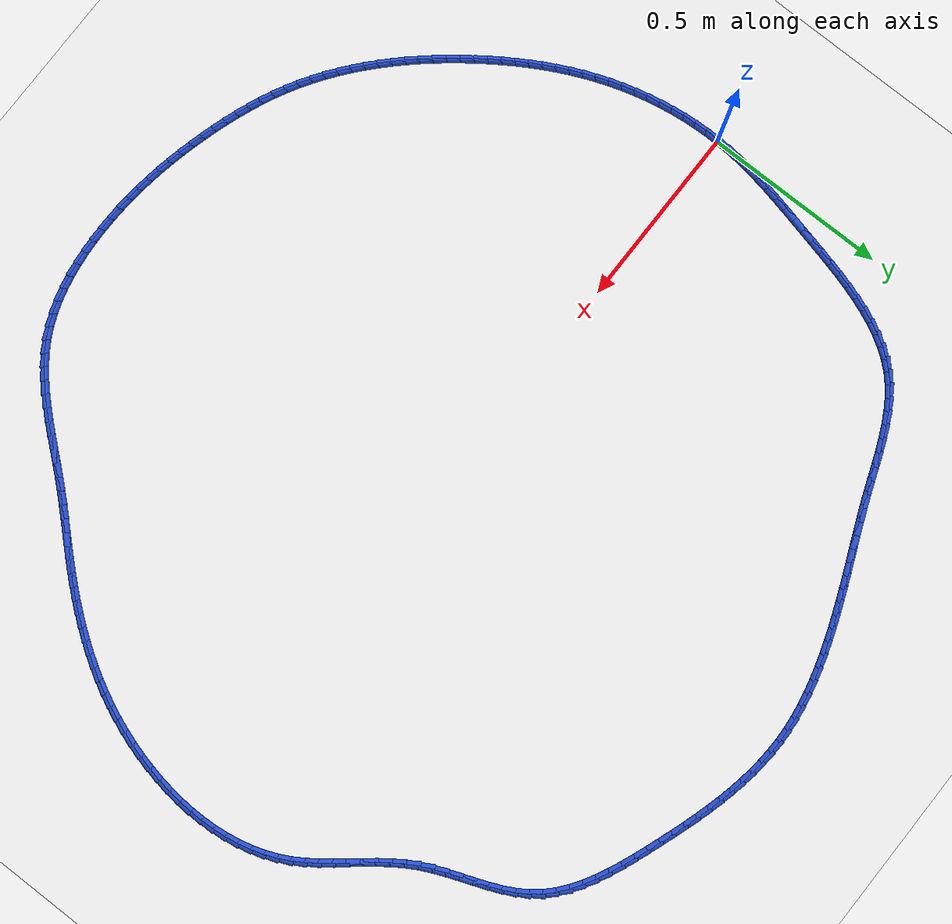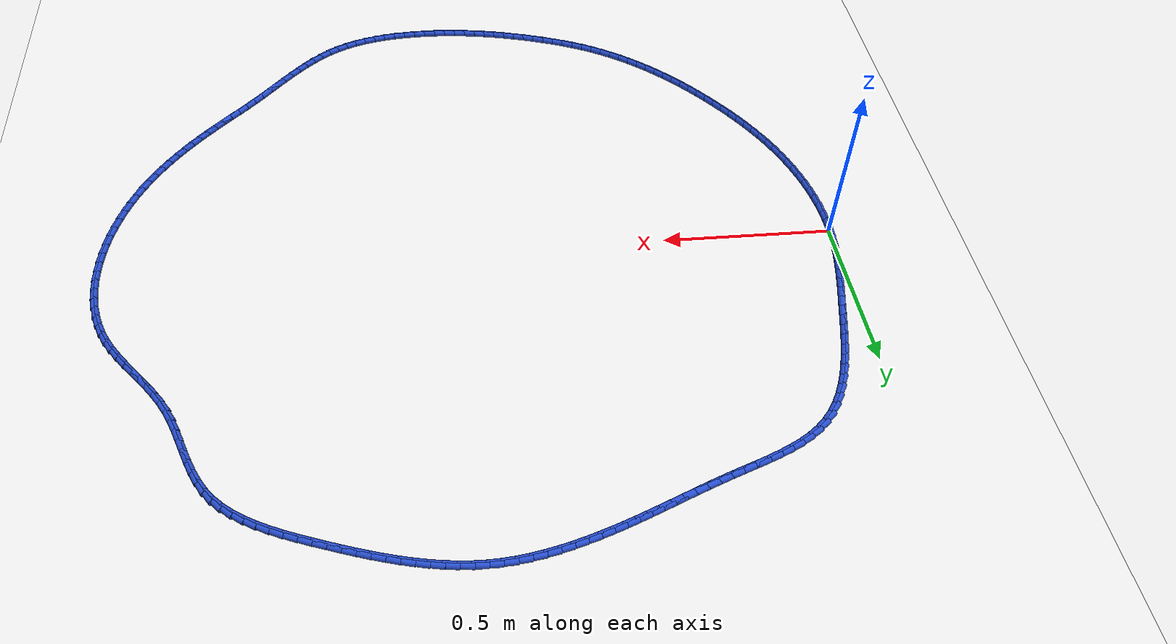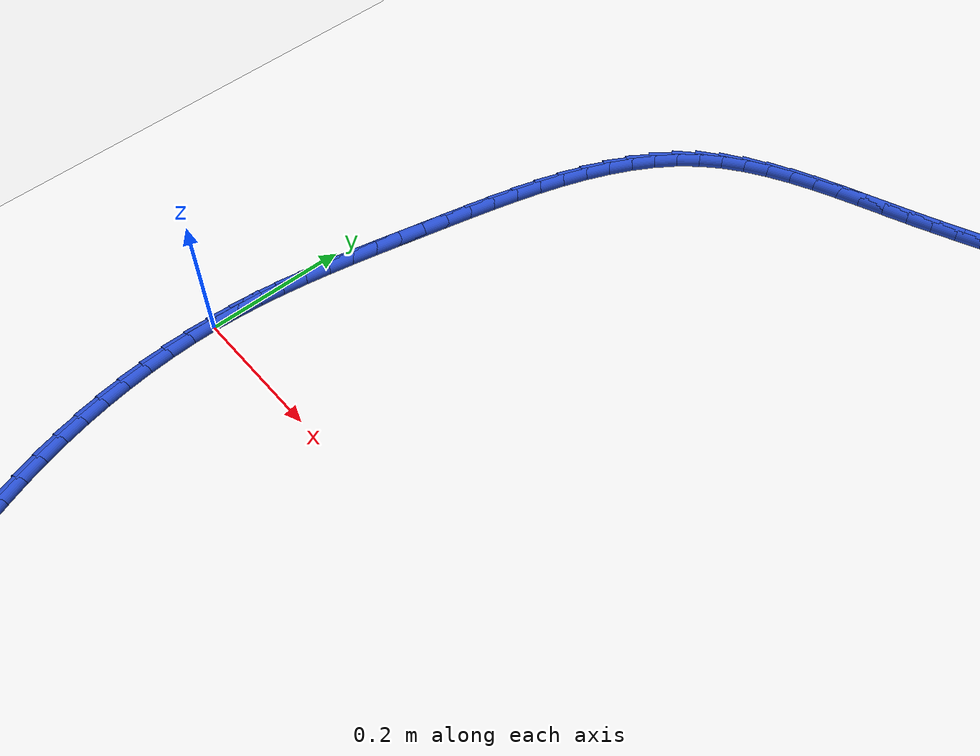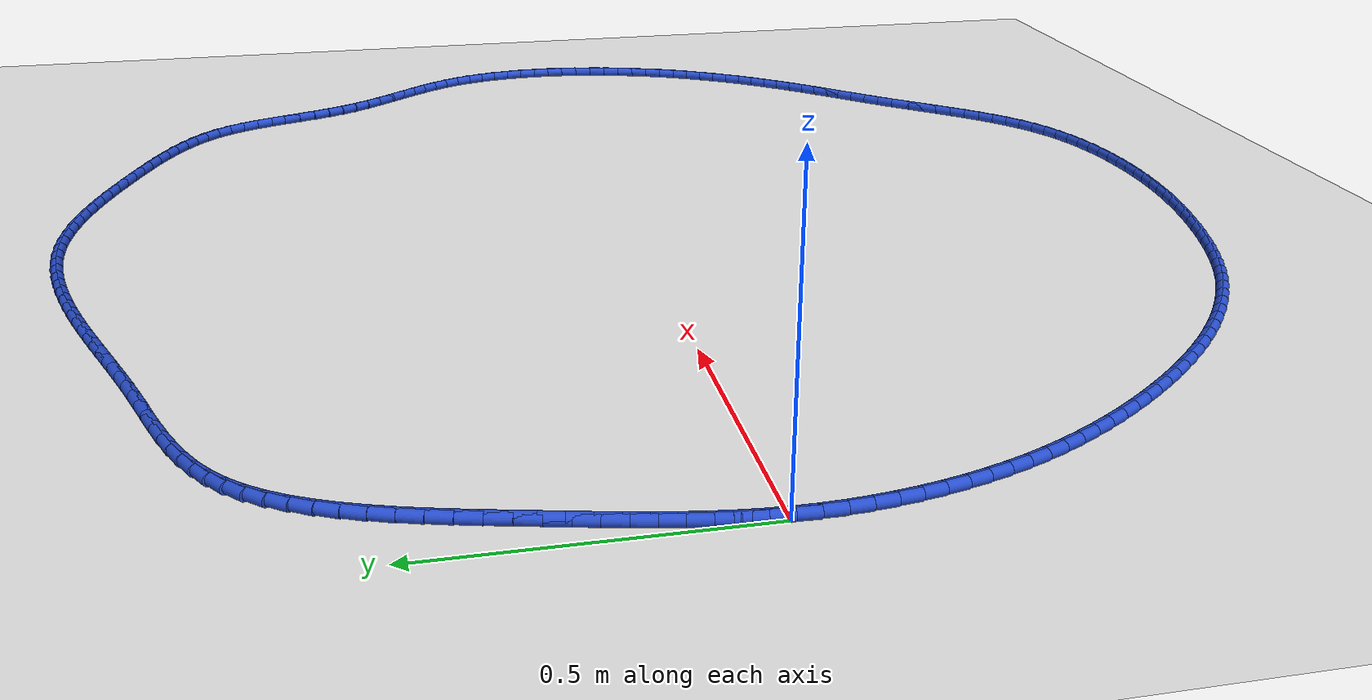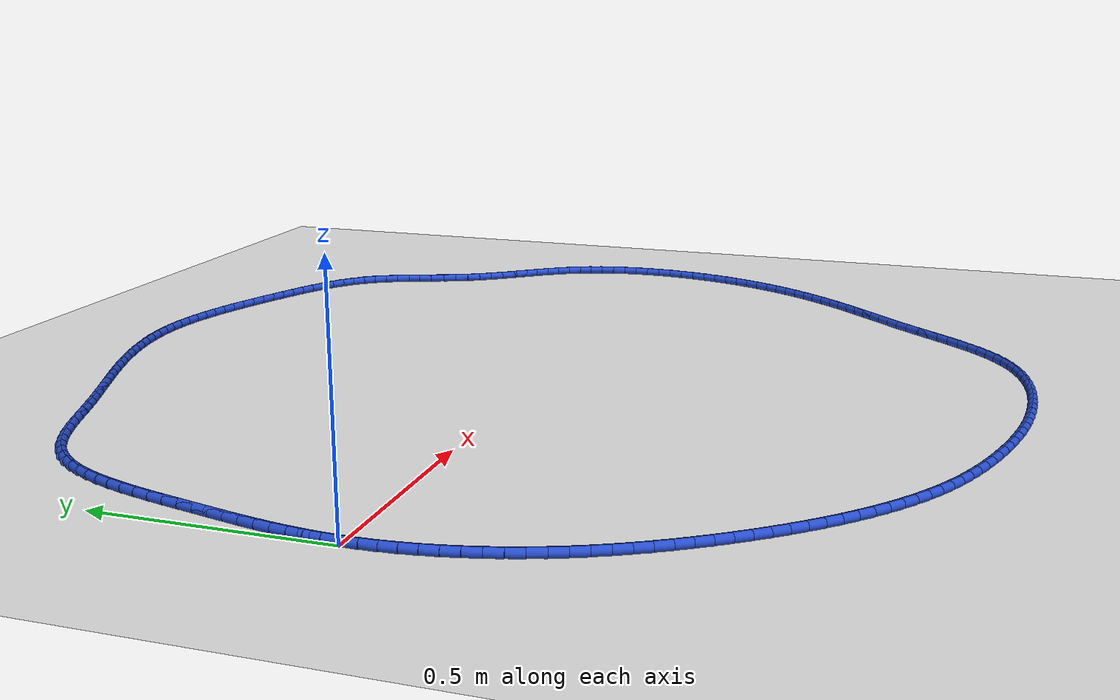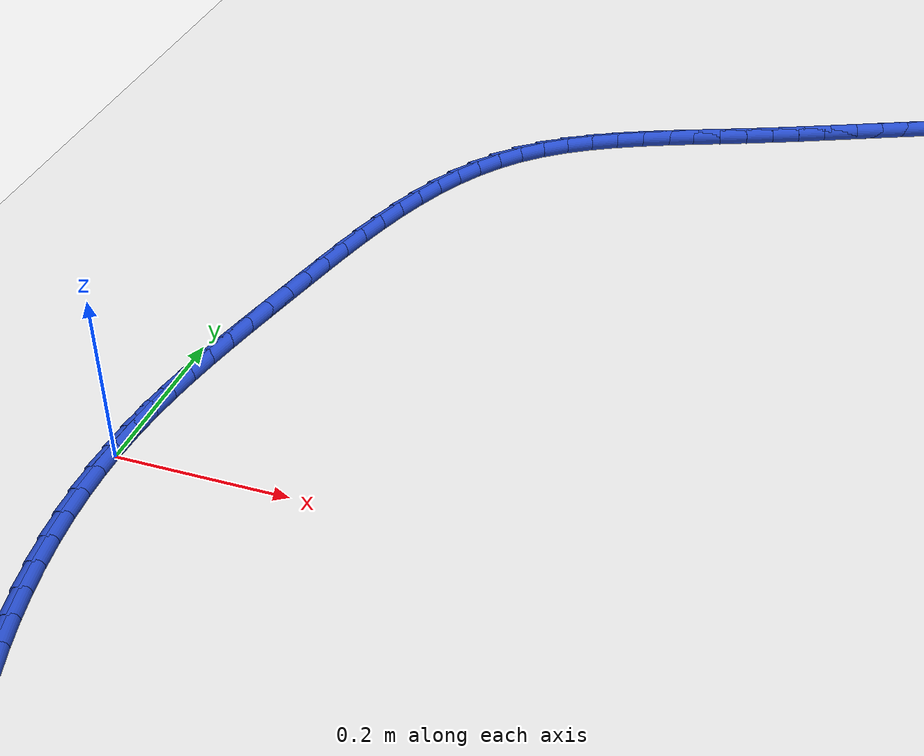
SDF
<sdf version="1.6">
 <world name="default">
  <light name="sun" type="directional">
   <pose>0 0 10 0 -0 0</pose>
   <diffuse>0.8 0.8 0.8 1</diffuse>
   <specular>0.2 0.2 0.2 1</specular>
   <attenuation>
    <range>1000</range>
    <constant>0.9</constant>
    <linear>0.01</linear>
    <quadratic>0.001</quadratic>
   </attenuation>
   <direction>-0.5 0.1 -0.9</direction>
  </light>
  <model name="ground_plane">
   <static>1</static>
   <link name="link">
    <collision name="collision">
     <geometry><plane><normal>0 0 1</normal><size>100 100</size></plane></geometry>
     <surface><friction><ode><mu>100</mu><mu2>50</mu2></ode></friction></surface>
    </collision>
    <visual name="visual">
     <cast_shadows>0</cast_shadows>
     <geometry><plane><normal>0 0 1</normal><size>100 100</size></plane></geometry>
     <material>
      <script><uri>file://media/materials/scripts/gazebo.material</uri><name>Gazebo/WhiteGlow</name></script>
     </material>
    </visual>
   </link>
  </model>
  <gravity>0 0 -9.8</gravity>
  <magnetic_field>6e-06 2.3e-05 -4.2e-05</magnetic_field>
  <atmosphere type="adiabatic"/>
  <physics name="default_physics" default="0" type="ode">
   <max_step_size>0.001</max_step_size>
   <real_time_factor>1</real_time_factor>
   <real_time_update_rate>1000</real_time_update_rate>
  </physics>
  <scene><ambient>0.4 0.4 0.4 1</ambient><background>0.7 0.7 0.7 1</background><shadows>1</shadows></scene>
  <spherical_coordinates>
   <surface_model>EARTH_WGS84</surface_model>
   <latitude_deg>0</latitude_deg>
   <longitude_deg>0</longitude_deg>
   <elevation>0</elevation>
   <heading_deg>0</heading_deg>
  </spherical_coordinates>
  <model name="line">
   <link name="link_0">
    <pose>-6.938893903907228e-18 -4.163336342344337e-17 0.01 0 1.57 1.5231848816671123</pose>
    <collision name="collision">
     <geometry><cylinder><radius>0.01</radius><length>0.08</length></cylinder></geometry>
    </collision>
    <visual name="visual">
     <material>
      <script><name>Gazebo/Blue</name><uri>file://media/materials/scripts/gazebo.material</uri></script>
     </material>
     <geometry><cylinder><radius>0.01</radius><length>0.08</length></cylinder></geometry>
    </visual>
   </link>
   <link name="link_1">
    <pose>0.0016453678152193493 0.03453212469598638 0.01 0 1.57 1.483026920934233</pose>
    <collision name="collision">
     <geometry><cylinder><radius>0.01</radius><length>0.08</length></cylinder></geometry>
    </collision>
    <visual name="visual">
     <material>
      <script><name>Gazebo/Blue</name><uri>file://media/materials/scripts/gazebo.material</uri></script>
     </material>
     <geometry><cylinder><radius>0.01</radius><length>0.08</length></cylinder></geometry>
    </visual>
   </link>
   <link name="link_2">
    <pose>0.004668144235646132 0.06888362163562825 0.01 0 1.57 1.4476217210021047</pose>
    <collision name="collision">
     <geometry><cylinder><radius>0.01</radius><length>0.08</length></cylinder></geometry>
    </collision>
    <visual name="visual">
     <material>
      <script><name>Gazebo/Blue</name><uri>file://media/materials/scripts/gazebo.material</uri></script>
     </material>
     <geometry><cylinder><radius>0.01</radius><length>0.08</length></cylinder></geometry>
    </visual>
   </link>
   <link name="link_3">
    <pose>0.008908018119011703 0.10313101950087082 0.01 0 1.57 1.4172315815503256</pose>
    <collision name="collision">
     <geometry><cylinder><radius>0.01</radius><length>0.08</length></cylinder></geometry>
    </collision>
    <visual name="visual">
     <material>
      <script><name>Gazebo/Blue</name><uri>file://media/materials/scripts/gazebo.material</uri></script>
     </material>
     <geometry><cylinder><radius>0.01</radius><length>0.08</length></cylinder></geometry>
    </visual>
   </link>
   <link name="link_4">
    <pose>0.014204678323047443 0.1373508469736592 0.01 0 1.57 1.392003799599424</pose>
    <collision name="collision">
     <geometry><cylinder><radius>0.01</radius><length>0.08</length></cylinder></geometry>
    </collision>
    <visual name="visual">
     <material>
      <script><name>Gazebo/Blue</name><uri>file://media/materials/scripts/gazebo.material</uri></script>
     </material>
     <geometry><cylinder><radius>0.01</radius><length>0.08</length></cylinder></geometry>
    </visual>
   </link>
   <link name="link_5">
    <pose>0.02039781370548471 0.1716196327359385 0.01 0 1.57 1.3719909108401365</pose>
    <collision name="collision">
     <geometry><cylinder><radius>0.01</radius><length>0.08</length></cylinder></geometry>
    </collision>
    <visual name="visual">
     <material>
      <script><name>Gazebo/Blue</name><uri>file://media/materials/scripts/gazebo.material</uri></script>
     </material>
     <geometry><cylinder><radius>0.01</radius><length>0.08</length></cylinder></geometry>
    </visual>
   </link>
   <link name="link_6">
    <pose>0.027327113124054878 0.20601390546965395 0.01 0 1.57 1.3571712182811437</pose>
    <collision name="collision">
     <geometry><cylinder><radius>0.01</radius><length>0.08</length></cylinder></geometry>
    </collision>
    <visual name="visual">
     <material>
      <script><name>Gazebo/Blue</name><uri>file://media/materials/scripts/gazebo.material</uri></script>
     </material>
     <geometry><cylinder><radius>0.01</radius><length>0.08</length></cylinder></geometry>
    </visual>
   </link>
   <link name="link_7">
    <pose>0.034832265436489304 0.2406101938567506 0.01 0 1.57 1.3474670817099204</pose>
    <collision name="collision">
     <geometry><cylinder><radius>0.01</radius><length>0.08</length></cylinder></geometry>
    </collision>
    <visual name="visual">
     <material>
      <script><name>Gazebo/Blue</name><uri>file://media/materials/scripts/gazebo.material</uri></script>
     </material>
     <geometry><cylinder><radius>0.01</radius><length>0.08</length></cylinder></geometry>
    </visual>
   </link>
   <link name="link_8">
    <pose>0.0427529595005194 0.2754850265791738 0.01 0 1.57 1.3427595870435172</pose>
    <collision name="collision">
     <geometry><cylinder><radius>0.01</radius><length>0.08</length></cylinder></geometry>
    </collision>
    <visual name="visual">
     <material>
      <script><name>Gazebo/Blue</name><uri>file://media/materials/scripts/gazebo.material</uri></script>
     </material>
     <geometry><cylinder><radius>0.01</radius><length>0.08</length></cylinder></geometry>
    </visual>
   </link>
   <link name="link_9">
    <pose>0.05092888417387649 0.3107149323188686 0.01 0 1.57 1.3424490822171338</pose>
    <collision name="collision">
     <geometry><cylinder><radius>0.01</radius><length>0.08</length></cylinder></geometry>
    </collision>
    <visual name="visual">
     <material>
      <script><name>Gazebo/Blue</name><uri>file://media/materials/scripts/gazebo.material</uri></script>
     </material>
     <geometry><cylinder><radius>0.01</radius><length>0.08</length></cylinder></geometry>
    </visual>
   </link>
   <link name="link_10">
    <pose>0.05921378283738589 0.3463641352428642 0.01 0 1.57 1.3398847619424221</pose>
    <collision name="collision">
     <geometry><cylinder><radius>0.01</radius><length>0.08</length></cylinder></geometry>
    </collision>
    <visual name="visual">
     <material>
      <script><name>Gazebo/Blue</name><uri>file://media/materials/scripts/gazebo.material</uri></script>
     </material>
     <geometry><cylinder><radius>0.01</radius><length>0.08</length></cylinder></geometry>
    </visual>
   </link>
   <link name="link_11">
    <pose>0.06766654538545468 0.38231725695754404 0.01 0 1.57 1.3301765616015284</pose>
    <collision name="collision">
     <geometry><cylinder><radius>0.01</radius><length>0.08</length></cylinder></geometry>
    </collision>
    <visual name="visual">
     <material>
      <script><name>Gazebo/Blue</name><uri>file://media/materials/scripts/gazebo.material</uri></script>
     </material>
     <geometry><cylinder><radius>0.01</radius><length>0.08</length></cylinder></geometry>
    </visual>
   </link>
   <link name="link_12">
    <pose>0.07650139031269201 0.41832293131180665 0.01 0 1.57 1.3131324652733358</pose>
    <collision name="collision">
     <geometry><cylinder><radius>0.01</radius><length>0.08</length></cylinder></geometry>
    </collision>
    <visual name="visual">
     <material>
      <script><name>Gazebo/Blue</name><uri>file://media/materials/scripts/gazebo.material</uri></script>
     </material>
     <geometry><cylinder><radius>0.01</radius><length>0.08</length></cylinder></geometry>
    </visual>
   </link>
   <link name="link_13">
    <pose>0.08593638472700423 0.454126422753867 0.01 0 1.57 1.2884683190787083</pose>
    <collision name="collision">
     <geometry><cylinder><radius>0.01</radius><length>0.08</length></cylinder></geometry>
    </collision>
    <visual name="visual">
     <material>
      <script><name>Gazebo/Blue</name><uri>file://media/materials/scripts/gazebo.material</uri></script>
     </material>
     <geometry><cylinder><radius>0.01</radius><length>0.08</length></cylinder></geometry>
    </visual>
   </link>
   <link name="link_14">
    <pose>0.09618959573629778 0.48947299573193964 0.01 0 1.57 1.255699086308736</pose>
    <collision name="collision">
     <geometry><cylinder><radius>0.01</radius><length>0.08</length></cylinder></geometry>
    </collision>
    <visual name="visual">
     <material>
      <script><name>Gazebo/Blue</name><uri>file://media/materials/scripts/gazebo.material</uri></script>
     </material>
     <geometry><cylinder><radius>0.01</radius><length>0.08</length></cylinder></geometry>
    </visual>
   </link>
   <link name="link_15">
    <pose>0.10747909044847909 0.5241079146942397 0.01 0 1.57 1.2141587710404707</pose>
    <collision name="collision">
     <geometry><cylinder><radius>0.01</radius><length>0.08</length></cylinder></geometry>
    </collision>
    <visual name="visual">
     <material>
      <script><name>Gazebo/Blue</name><uri>file://media/materials/scripts/gazebo.material</uri></script>
     </material>
     <geometry><cylinder><radius>0.01</radius><length>0.08</length></cylinder></geometry>
    </visual>
   </link>
   <link name="link_16">
    <pose>0.12002293597145462 0.557776444088982 0.01 0 1.57 1.163037955421958</pose>
    <collision name="collision">
     <geometry><cylinder><radius>0.01</radius><length>0.08</length></cylinder></geometry>
    </collision>
    <visual name="visual">
     <material>
      <script><name>Gazebo/Blue</name><uri>file://media/materials/scripts/gazebo.material</uri></script>
     </material>
     <geometry><cylinder><radius>0.01</radius><length>0.08</length></cylinder></geometry>
    </visual>
   </link>
   <link name="link_17">
    <pose>0.13403919941313078 0.5902238483643812 0.01 0 1.57 1.1014571595796385</pose>
    <collision name="collision">
     <geometry><cylinder><radius>0.01</radius><length>0.08</length></cylinder></geometry>
    </collision>
    <visual name="visual">
     <material>
      <script><name>Gazebo/Blue</name><uri>file://media/materials/scripts/gazebo.material</uri></script>
     </material>
     <geometry><cylinder><radius>0.01</radius><length>0.08</length></cylinder></geometry>
    </visual>
   </link>
   <link name="link_18">
    <pose>0.14974594788141396 0.6211953919686523 0.01 0 1.57 1.0286000902121475</pose>
    <collision name="collision">
     <geometry><cylinder><radius>0.01</radius><length>0.08</length></cylinder></geometry>
    </collision>
    <visual name="visual">
     <material>
      <script><name>Gazebo/Blue</name><uri>file://media/materials/scripts/gazebo.material</uri></script>
     </material>
     <geometry><cylinder><radius>0.01</radius><length>0.08</length></cylinder></geometry>
    </visual>
   </link>
   <link name="link_19">
    <pose>0.16736124848421058 0.6504363393500101 0.01 0 1.57 0.9439308126309682</pose>
    <collision name="collision">
     <geometry><cylinder><radius>0.01</radius><length>0.08</length></cylinder></geometry>
    </collision>
    <visual name="visual">
     <material>
      <script><name>Gazebo/Blue</name><uri>file://media/materials/scripts/gazebo.material</uri></script>
     </material>
     <geometry><cylinder><radius>0.01</radius><length>0.08</length></cylinder></geometry>
    </visual>
   </link>
   <link name="link_20">
    <pose>0.1871031683294271 0.6776919549566693 0.01 0 1.57 0.847500964042031</pose>
    <collision name="collision">
     <geometry><cylinder><radius>0.01</radius><length>0.08</length></cylinder></geometry>
    </collision>
    <visual name="visual">
     <material>
      <script><name>Gazebo/Blue</name><uri>file://media/materials/scripts/gazebo.material</uri></script>
     </material>
     <geometry><cylinder><radius>0.01</radius><length>0.08</length></cylinder></geometry>
    </visual>
   </link>
   <link name="link_21">
    <pose>0.20918977452496995 0.7027075032368449 0.01 0 1.57 0.741124443735339</pose>
    <collision name="collision">
     <geometry><cylinder><radius>0.01</radius><length>0.08</length></cylinder></geometry>
    </collision>
    <visual name="visual">
     <material>
      <script><name>Gazebo/Blue</name><uri>file://media/materials/scripts/gazebo.material</uri></script>
     </material>
     <geometry><cylinder><radius>0.01</radius><length>0.08</length></cylinder></geometry>
    </visual>
   </link>
   <link name="link_22">
    <pose>0.2338199418164173 0.725247889067673 0.01 0 1.57 0.6399884802421354</pose>
    <collision name="collision">
     <geometry><cylinder><radius>0.01</radius><length>0.08</length></cylinder></geometry>
    </collision>
    <visual name="visual">
     <material>
      <script><name>Gazebo/Blue</name><uri>file://media/materials/scripts/gazebo.material</uri></script>
     </material>
     <geometry><cylinder><radius>0.01</radius><length>0.08</length></cylinder></geometry>
    </visual>
   </link>
   <link name="link_23">
    <pose>0.2608817282276211 0.7453960904027626 0.01 0 1.57 0.5559017023129282</pose>
    <collision name="collision">
     <geometry><cylinder><radius>0.01</radius><length>0.08</length></cylinder></geometry>
    </collision>
    <visual name="visual">
     <material>
      <script><name>Gazebo/Blue</name><uri>file://media/materials/scripts/gazebo.material</uri></script>
     </material>
     <geometry><cylinder><radius>0.01</radius><length>0.08</length></cylinder></geometry>
    </visual>
   </link>
   <link name="link_24">
    <pose>0.2900112252018906 0.7634929342103997 0.01 0 1.57 0.4887742874849566</pose>
    <collision name="collision">
     <geometry><cylinder><radius>0.01</radius><length>0.08</length></cylinder></geometry>
    </collision>
    <visual name="visual">
     <material>
      <script><name>Gazebo/Blue</name><uri>file://media/materials/scripts/gazebo.material</uri></script>
     </material>
     <geometry><cylinder><radius>0.01</radius><length>0.08</length></cylinder></geometry>
    </visual>
   </link>
   <link name="link_25">
    <pose>0.32083726465603 0.7798866764669238 0.01 0 1.57 0.437518248125738</pose>
    <collision name="collision">
     <geometry><cylinder><radius>0.01</radius><length>0.08</length></cylinder></geometry>
    </collision>
    <visual name="visual">
     <material>
      <script><name>Gazebo/Blue</name><uri>file://media/materials/scripts/gazebo.material</uri></script>
     </material>
     <geometry><cylinder><radius>0.01</radius><length>0.08</length></cylinder></geometry>
    </visual>
   </link>
   <link name="link_26">
    <pose>0.352988678506844 0.7949255731486736 0.01 0 1.57 0.4009087303809482</pose>
    <collision name="collision">
     <geometry><cylinder><radius>0.01</radius><length>0.08</length></cylinder></geometry>
    </collision>
    <visual name="visual">
     <material>
      <script><name>Gazebo/Blue</name><uri>file://media/materials/scripts/gazebo.material</uri></script>
     </material>
     <geometry><cylinder><radius>0.01</radius><length>0.08</length></cylinder></geometry>
    </visual>
   </link>
   <link name="link_27">
    <pose>0.38609429867113715 0.8089578802319891 0.01 0 1.57 0.37790662754015253</pose>
    <collision name="collision">
     <geometry><cylinder><radius>0.01</radius><length>0.08</length></cylinder></geometry>
    </collision>
    <visual name="visual">
     <material>
      <script><name>Gazebo/Blue</name><uri>file://media/materials/scripts/gazebo.material</uri></script>
     </material>
     <geometry><cylinder><radius>0.01</radius><length>0.08</length></cylinder></geometry>
    </visual>
   </link>
   <link name="link_28">
    <pose>0.41978295706571406 0.8223318536932097 0.01 0 1.57 0.3678220270332629</pose>
    <collision name="collision">
     <geometry><cylinder><radius>0.01</radius><length>0.08</length></cylinder></geometry>
    </collision>
    <visual name="visual">
     <material>
      <script><name>Gazebo/Blue</name><uri>file://media/materials/scripts/gazebo.material</uri></script>
     </material>
     <geometry><cylinder><radius>0.01</radius><length>0.08</length></cylinder></geometry>
    </visual>
   </link>
   <link name="link_29">
    <pose>0.4536834856073794 0.8353957495086747 0.01 0 1.57 0.37038830947877116</pose>
    <collision name="collision">
     <geometry><cylinder><radius>0.01</radius><length>0.08</length></cylinder></geometry>
    </collision>
    <visual name="visual">
     <material>
      <script><name>Gazebo/Blue</name><uri>file://media/materials/scripts/gazebo.material</uri></script>
     </material>
     <geometry><cylinder><radius>0.01</radius><length>0.08</length></cylinder></geometry>
    </visual>
   </link>
   <link name="link_30">
    <pose>0.48742472968225314 0.8484978104731602 0.01 0 1.57 0.38260862523265976</pose>
    <collision name="collision">
     <geometry><cylinder><radius>0.01</radius><length>0.08</length></cylinder></geometry>
    </collision>
    <visual name="visual">
     <material>
      <script><name>Gazebo/Blue</name><uri>file://media/materials/scripts/gazebo.material</uri></script>
     </material>
     <geometry><cylinder><radius>0.01</radius><length>0.08</length></cylinder></geometry>
    </visual>
   </link>
   <link name="link_31">
    <pose>0.5207246611274198 0.8618990569873597 0.01 0 1.57 0.39394718605487383</pose>
    <collision name="collision">
     <geometry><cylinder><radius>0.01</radius><length>0.08</length></cylinder></geometry>
    </collision>
    <visual name="visual">
     <material>
      <script><name>Gazebo/Blue</name><uri>file://media/materials/scripts/gazebo.material</uri></script>
     </material>
     <geometry><cylinder><radius>0.01</radius><length>0.08</length></cylinder></geometry>
    </visual>
   </link>
   <link name="link_32">
    <pose>0.5536025665972087 0.8755656317871592 0.01 0 1.57 0.40204795960847106</pose>
    <collision name="collision">
     <geometry><cylinder><radius>0.01</radius><length>0.08</length></cylinder></geometry>
    </collision>
    <visual name="visual">
     <material>
      <script><name>Gazebo/Blue</name><uri>file://media/materials/scripts/gazebo.material</uri></script>
     </material>
     <geometry><cylinder><radius>0.01</radius><length>0.08</length></cylinder></geometry>
    </visual>
   </link>
   <link name="link_33">
    <pose>0.5861413446970477 0.8894014246340826 0.01 0 1.57 0.4068142637108959</pose>
    <collision name="collision">
     <geometry><cylinder><radius>0.01</radius><length>0.08</length></cylinder></geometry>
    </collision>
    <visual name="visual">
     <material>
      <script><name>Gazebo/Blue</name><uri>file://media/materials/scripts/gazebo.material</uri></script>
     </material>
     <geometry><cylinder><radius>0.01</radius><length>0.08</length></cylinder></geometry>
    </visual>
   </link>
   <link name="link_34">
    <pose>0.6184238940323642 0.9033103252896527 0.01 0 1.57 0.40817089300165244</pose>
    <collision name="collision">
     <geometry><cylinder><radius>0.01</radius><length>0.08</length></cylinder></geometry>
    </collision>
    <visual name="visual">
     <material>
      <script><name>Gazebo/Blue</name><uri>file://media/materials/scripts/gazebo.material</uri></script>
     </material>
     <geometry><cylinder><radius>0.01</radius><length>0.08</length></cylinder></geometry>
    </visual>
   </link>
   <link name="link_35">
    <pose>0.6505331132085849 0.9171962235153922 0.01 0 1.57 0.4060639736785271</pose>
    <collision name="collision">
     <geometry><cylinder><radius>0.01</radius><length>0.08</length></cylinder></geometry>
    </collision>
    <visual name="visual">
     <material>
      <script><name>Gazebo/Blue</name><uri>file://media/materials/scripts/gazebo.material</uri></script>
     </material>
     <geometry><cylinder><radius>0.01</radius><length>0.08</length></cylinder></geometry>
    </visual>
   </link>
   <link name="link_36">
    <pose>0.6825519008311373 0.9309630090728247 0.01 0 1.57 0.4004616030045988</pose>
    <collision name="collision">
     <geometry><cylinder><radius>0.01</radius><length>0.08</length></cylinder></geometry>
    </collision>
    <visual name="visual">
     <material>
      <script><name>Gazebo/Blue</name><uri>file://media/materials/scripts/gazebo.material</uri></script>
     </material>
     <geometry><cylinder><radius>0.01</radius><length>0.08</length></cylinder></geometry>
    </visual>
   </link>
   <link name="link_37">
    <pose>0.7145631555054484 0.944514571723473 0.01 0 1.57 0.39135538824786836</pose>
    <collision name="collision">
     <geometry><cylinder><radius>0.01</radius><length>0.08</length></cylinder></geometry>
    </collision>
    <visual name="visual">
     <material>
      <script><name>Gazebo/Blue</name><uri>file://media/materials/scripts/gazebo.material</uri></script>
     </material>
     <geometry><cylinder><radius>0.01</radius><length>0.08</length></cylinder></geometry>
    </visual>
   </link>
   <link name="link_38">
    <pose>0.7466497758369455 0.9577548012288601 0.01 0 1.57 0.3787629009597183</pose>
    <collision name="collision">
     <geometry><cylinder><radius>0.01</radius><length>0.08</length></cylinder></geometry>
    </collision>
    <visual name="visual">
     <material>
      <script><name>Gazebo/Blue</name><uri>file://media/materials/scripts/gazebo.material</uri></script>
     </material>
     <geometry><cylinder><radius>0.01</radius><length>0.08</length></cylinder></geometry>
    </visual>
   </link>
   <link name="link_39">
    <pose>0.7788946604310563 0.9705875873505094 0.01 0 1.57 0.3627309471428266</pose>
    <collision name="collision">
     <geometry><cylinder><radius>0.01</radius><length>0.08</length></cylinder></geometry>
    </collision>
    <visual name="visual">
     <material>
      <script><name>Gazebo/Blue</name><uri>file://media/materials/scripts/gazebo.material</uri></script>
     </material>
     <geometry><cylinder><radius>0.01</radius><length>0.08</length></cylinder></geometry>
    </visual>
   </link>
   <link name="link_40">
    <pose>0.8113807078932072 0.9829168198499435 0.01 0 1.57 0.34333942229906256</pose>
    <collision name="collision">
     <geometry><cylinder><radius>0.01</radius><length>0.08</length></cylinder></geometry>
    </collision>
    <visual name="visual">
     <material>
      <script><name>Gazebo/Blue</name><uri>file://media/materials/scripts/gazebo.material</uri></script>
     </material>
     <geometry><cylinder><radius>0.01</radius><length>0.08</length></cylinder></geometry>
    </visual>
   </link>
   <link name="link_41">
    <pose>0.8441908168288261 0.994646388488686 0.01 0 1.57 0.3207053779769576</pose>
    <collision name="collision">
     <geometry><cylinder><radius>0.01</radius><length>0.08</length></cylinder></geometry>
    </collision>
    <visual name="visual">
     <material>
      <script><name>Gazebo/Blue</name><uri>file://media/materials/scripts/gazebo.material</uri></script>
     </material>
     <geometry><cylinder><radius>0.01</radius><length>0.08</length></cylinder></geometry>
    </visual>
   </link>
   <link name="link_42">
    <pose>0.8774078858433402 1.00568018302826 0.01 0 1.57 0.29482234900867565</pose>
    <collision name="collision">
     <geometry><cylinder><radius>0.01</radius><length>0.08</length></cylinder></geometry>
    </collision>
    <visual name="visual">
     <material>
      <script><name>Gazebo/Blue</name><uri>file://media/materials/scripts/gazebo.material</uri></script>
     </material>
     <geometry><cylinder><radius>0.01</radius><length>0.08</length></cylinder></geometry>
    </visual>
   </link>
   <link name="link_43">
    <pose>0.9110902130092232 1.0159085686106593 0.01 0 1.57 0.26489532597117177</pose>
    <collision name="collision">
     <geometry><cylinder><radius>0.01</radius><length>0.08</length></cylinder></geometry>
    </collision>
    <visual name="visual">
     <material>
      <script><name>Gazebo/Blue</name><uri>file://media/materials/scripts/gazebo.material</uri></script>
     </material>
     <geometry><cylinder><radius>0.01</radius><length>0.08</length></cylinder></geometry>
    </visual>
   </link>
   <link name="link_44">
    <pose>0.945172915394058 1.0251541892342952 0.01 0 1.57 0.23040157071232448</pose>
    <collision name="collision">
     <geometry><cylinder><radius>0.01</radius><length>0.08</length></cylinder></geometry>
    </collision>
    <visual name="visual">
     <material>
      <script><name>Gazebo/Blue</name><uri>file://media/materials/scripts/gazebo.material</uri></script>
     </material>
     <geometry><cylinder><radius>0.01</radius><length>0.08</length></cylinder></geometry>
    </visual>
   </link>
   <link name="link_45">
    <pose>0.9795526351108578 1.0332185365460047 0.01 0 1.57 0.19098760197456974</pose>
    <collision name="collision">
     <geometry><cylinder><radius>0.01</radius><length>0.08</length></cylinder></geometry>
    </collision>
    <visual name="visual">
     <material>
      <script><name>Gazebo/Blue</name><uri>file://media/materials/scripts/gazebo.material</uri></script>
     </material>
     <geometry><cylinder><radius>0.01</radius><length>0.08</length></cylinder></geometry>
    </visual>
   </link>
   <link name="link_46">
    <pose>1.014126001371406 1.039903095099924 0.01 0 1.57 0.1462567880832043</pose>
    <collision name="collision">
     <geometry><cylinder><radius>0.01</radius><length>0.08</length></cylinder></geometry>
    </collision>
    <visual name="visual">
     <material>
      <script><name>Gazebo/Blue</name><uri>file://media/materials/scripts/gazebo.material</uri></script>
     </material>
     <geometry><cylinder><radius>0.01</radius><length>0.08</length></cylinder></geometry>
    </visual>
   </link>
   <link name="link_47">
    <pose>1.0487896433874848 1.045009349450188 0.01 0 1.57 0.09579198619954958</pose>
    <collision name="collision">
     <geometry><cylinder><radius>0.01</radius><length>0.08</length></cylinder></geometry>
    </collision>
    <visual name="visual">
     <material>
      <script><name>Gazebo/Blue</name><uri>file://media/materials/scripts/gazebo.material</uri></script>
     </material>
     <geometry><cylinder><radius>0.01</radius><length>0.08</length></cylinder></geometry>
    </visual>
   </link>
   <link name="link_48">
    <pose>1.0834401903708775 1.0483387841509324 0.01 0 1.57 0.03996815017787153</pose>
    <collision name="collision">
     <geometry><cylinder><radius>0.01</radius><length>0.08</length></cylinder></geometry>
    </collision>
    <visual name="visual">
     <material>
      <script><name>Gazebo/Blue</name><uri>file://media/materials/scripts/gazebo.material</uri></script>
     </material>
     <geometry><cylinder><radius>0.01</radius><length>0.08</length></cylinder></geometry>
    </visual>
   </link>
   <link name="link_49">
    <pose>1.117984678842834 1.0497201991141853 0.01 0 1.57 -0.015351555038040691</pose>
    <collision name="collision">
     <geometry><cylinder><radius>0.01</radius><length>0.08</length></cylinder></geometry>
    </collision>
    <visual name="visual">
     <material>
      <script><name>Gazebo/Blue</name><uri>file://media/materials/scripts/gazebo.material</uri></script>
     </material>
     <geometry><cylinder><radius>0.01</radius><length>0.08</length></cylinder></geometry>
    </visual>
   </link>
   <link name="link_50">
    <pose>1.1524098833289977 1.0491916771732033 0.01 0 1.57 -0.06700196114378378</pose>
    <collision name="collision">
     <geometry><cylinder><radius>0.01</radius><length>0.08</length></cylinder></geometry>
    </collision>
    <visual name="visual">
     <material>
      <script><name>Gazebo/Blue</name><uri>file://media/materials/scripts/gazebo.material</uri></script>
     </material>
     <geometry><cylinder><radius>0.01</radius><length>0.08</length></cylinder></geometry>
    </visual>
   </link>
   <link name="link_51">
    <pose>1.186739451871221 1.0468880805733638 0.01 0 1.57 -0.11460189729281117</pose>
    <collision name="collision">
     <geometry><cylinder><radius>0.01</radius><length>0.08</length></cylinder></geometry>
    </collision>
    <visual name="visual">
     <material>
      <script><name>Gazebo/Blue</name><uri>file://media/materials/scripts/gazebo.material</uri></script>
     </material>
     <geometry><cylinder><radius>0.01</radius><length>0.08</length></cylinder></geometry>
    </visual>
   </link>
   <link name="link_52">
    <pose>1.2209972321921216 1.0429447956485753 0.01 0 1.57 -0.15791448755461227</pose>
    <collision name="collision">
     <geometry><cylinder><radius>0.01</radius><length>0.08</length></cylinder></geometry>
    </collision>
    <visual name="visual">
     <material>
      <script><name>Gazebo/Blue</name><uri>file://media/materials/scripts/gazebo.material</uri></script>
     </material>
     <geometry><cylinder><radius>0.01</radius><length>0.08</length></cylinder></geometry>
    </visual>
   </link>
   <link name="link_53">
    <pose>1.2552070720143158 1.0374972087327463 0.01 0 1.57 -0.1968147613375584</pose>
    <collision name="collision">
     <geometry><cylinder><radius>0.01</radius><length>0.08</length></cylinder></geometry>
    </collision>
    <visual name="visual">
     <material>
      <script><name>Gazebo/Blue</name><uri>file://media/materials/scripts/gazebo.material</uri></script>
     </material>
     <geometry><cylinder><radius>0.01</radius><length>0.08</length></cylinder></geometry>
    </visual>
   </link>
   <link name="link_54">
    <pose>1.2893928190604216 1.0306807061597845 0.01 0 1.57 -0.23126761936936419</pose>
    <collision name="collision">
     <geometry><cylinder><radius>0.01</radius><length>0.08</length></cylinder></geometry>
    </collision>
    <visual name="visual">
     <material>
      <script><name>Gazebo/Blue</name><uri>file://media/materials/scripts/gazebo.material</uri></script>
     </material>
     <geometry><cylinder><radius>0.01</radius><length>0.08</length></cylinder></geometry>
    </visual>
   </link>
   <link name="link_55">
    <pose>1.323578321053056 1.022630674263598 0.01 0 1.57 -0.26130492769246394</pose>
    <collision name="collision">
     <geometry><cylinder><radius>0.01</radius><length>0.08</length></cylinder></geometry>
    </collision>
    <visual name="visual">
     <material>
      <script><name>Gazebo/Blue</name><uri>file://media/materials/scripts/gazebo.material</uri></script>
     </material>
     <geometry><cylinder><radius>0.01</radius><length>0.08</length></cylinder></geometry>
    </visual>
   </link>
   <link name="link_56">
    <pose>1.3577874257148355 1.013482499378095 0.01 0 1.57 -0.28700427061733946</pose>
    <collision name="collision">
     <geometry><cylinder><radius>0.01</radius><length>0.08</length></cylinder></geometry>
    </collision>
    <visual name="visual">
     <material>
      <script><name>Gazebo/Blue</name><uri>file://media/materials/scripts/gazebo.material</uri></script>
     </material>
     <geometry><cylinder><radius>0.01</radius><length>0.08</length></cylinder></geometry>
    </visual>
   </link>
   <link name="link_57">
    <pose>1.3920439807683773 1.0033715678371835 0.01 0 1.57 -0.3084707622308271</pose>
    <collision name="collision">
     <geometry><cylinder><radius>0.01</radius><length>0.08</length></cylinder></geometry>
    </collision>
    <visual name="visual">
     <material>
      <script><name>Gazebo/Blue</name><uri>file://media/materials/scripts/gazebo.material</uri></script>
     </material>
     <geometry><cylinder><radius>0.01</radius><length>0.08</length></cylinder></geometry>
    </visual>
   </link>
   <link name="link_58">
    <pose>1.4263718339362992 0.9924332659747714 0.01 0 1.57 -0.3258224332430204</pose>
    <collision name="collision">
     <geometry><cylinder><radius>0.01</radius><length>0.08</length></cylinder></geometry>
    </collision>
    <visual name="visual">
     <material>
      <script><name>Gazebo/Blue</name><uri>file://media/materials/scripts/gazebo.material</uri></script>
     </material>
     <geometry><cylinder><radius>0.01</radius><length>0.08</length></cylinder></geometry>
    </visual>
   </link>
   <link name="link_59">
    <pose>1.4607948329412177 0.9808029801247676 0.01 0 1.57 -0.3391791329569963</pose>
    <collision name="collision">
     <geometry><cylinder><radius>0.01</radius><length>0.08</length></cylinder></geometry>
    </collision>
    <visual name="visual">
     <material>
      <script><name>Gazebo/Blue</name><uri>file://media/materials/scripts/gazebo.material</uri></script>
     </material>
     <geometry><cylinder><radius>0.01</radius><length>0.08</length></cylinder></geometry>
    </visual>
   </link>
   <link name="link_60">
    <pose>1.4953368255057502 0.9686160966210792 0.01 0 1.57 -0.3489738257213363</pose>
    <collision name="collision">
     <geometry><cylinder><radius>0.01</radius><length>0.08</length></cylinder></geometry>
    </collision>
    <visual name="visual">
     <material>
      <script><name>Gazebo/Blue</name><uri>file://media/materials/scripts/gazebo.material</uri></script>
     </material>
     <geometry><cylinder><radius>0.01</radius><length>0.08</length></cylinder></geometry>
    </visual>
   </link>
   <link name="link_61">
    <pose>1.530012348448656 0.955998852021136 0.01 0 1.57 -0.3619204385596227</pose>
    <collision name="collision">
     <geometry><cylinder><radius>0.01</radius><length>0.08</length></cylinder></geometry>
    </collision>
    <visual name="visual">
     <material>
      <script><name>Gazebo/Blue</name><uri>file://media/materials/scripts/gazebo.material</uri></script>
     </material>
     <geometry><cylinder><radius>0.01</radius><length>0.08</length></cylinder></geometry>
    </visual>
   </link>
   <link name="link_62">
    <pose>1.564642933378126 0.9428878176723186 0.01 0 1.57 -0.38445339315399024</pose>
    <collision name="collision">
     <geometry><cylinder><radius>0.01</radius><length>0.08</length></cylinder></geometry>
    </collision>
    <visual name="visual">
     <material>
      <script><name>Gazebo/Blue</name><uri>file://media/materials/scripts/gazebo.material</uri></script>
     </material>
     <geometry><cylinder><radius>0.01</radius><length>0.08</length></cylinder></geometry>
    </visual>
   </link>
   <link name="link_63">
    <pose>1.5988681709228885 0.9290407724739453 0.01 0 1.57 -0.4173383969233208</pose>
    <collision name="collision">
     <geometry><cylinder><radius>0.01</radius><length>0.08</length></cylinder></geometry>
    </collision>
    <visual name="visual">
     <material>
      <script><name>Gazebo/Blue</name><uri>file://media/materials/scripts/gazebo.material</uri></script>
     </material>
     <geometry><cylinder><radius>0.01</radius><length>0.08</length></cylinder></geometry>
    </visual>
   </link>
   <link name="link_64">
    <pose>1.6323205560718876 0.9142085224772634 0.01 0 1.57 -0.4614326083498727</pose>
    <collision name="collision">
     <geometry><cylinder><radius>0.01</radius><length>0.08</length></cylinder></geometry>
    </collision>
    <visual name="visual">
     <material>
      <script><name>Gazebo/Blue</name><uri>file://media/materials/scripts/gazebo.material</uri></script>
     </material>
     <geometry><cylinder><radius>0.01</radius><length>0.08</length></cylinder></geometry>
    </visual>
   </link>
   <link name="link_65">
    <pose>1.6646325838140654 0.8981418737335178 0.01 0 1.57 -0.5178692333564154</pose>
    <collision name="collision">
     <geometry><cylinder><radius>0.01</radius><length>0.08</length></cylinder></geometry>
    </collision>
    <visual name="visual">
     <material>
      <script><name>Gazebo/Blue</name><uri>file://media/materials/scripts/gazebo.material</uri></script>
     </material>
     <geometry><cylinder><radius>0.01</radius><length>0.08</length></cylinder></geometry>
    </visual>
   </link>
   <link name="link_66">
    <pose>1.6954367491383648 0.880591632293956 0.01 0 1.57 -0.5879347026942255</pose>
    <collision name="collision">
     <geometry><cylinder><radius>0.01</radius><length>0.08</length></cylinder></geometry>
    </collision>
    <visual name="visual">
     <material>
      <script><name>Gazebo/Blue</name><uri>file://media/materials/scripts/gazebo.material</uri></script>
     </material>
     <geometry><cylinder><radius>0.01</radius><length>0.08</length></cylinder></geometry>
    </visual>
   </link>
   <link name="link_67">
    <pose>1.7243655470337278 0.8613086042098229 0.01 0 1.57 -0.6728247970018595</pose>
    <collision name="collision">
     <geometry><cylinder><radius>0.01</radius><length>0.08</length></cylinder></geometry>
    </collision>
    <visual name="visual">
     <material>
      <script><name>Gazebo/Blue</name><uri>file://media/materials/scripts/gazebo.material</uri></script>
     </material>
     <geometry><cylinder><radius>0.01</radius><length>0.08</length></cylinder></geometry>
    </visual>
   </link>
   <link name="link_68">
    <pose>1.751051472489097 0.8400435955323653 0.01 0 1.57 -0.7732200036332522</pose>
    <collision name="collision">
     <geometry><cylinder><radius>0.01</radius><length>0.08</length></cylinder></geometry>
    </collision>
    <visual name="visual">
     <material>
      <script><name>Gazebo/Blue</name><uri>file://media/materials/scripts/gazebo.material</uri></script>
     </material>
     <geometry><cylinder><radius>0.01</radius><length>0.08</length></cylinder></geometry>
    </visual>
   </link>
   <link name="link_69">
    <pose>1.7751270204934155 0.816547412312829 0.01 0 1.57 -0.8884469797744952</pose>
    <collision name="collision">
     <geometry><cylinder><radius>0.01</radius><length>0.08</length></cylinder></geometry>
    </collision>
    <visual name="visual">
     <material>
      <script><name>Gazebo/Blue</name><uri>file://media/materials/scripts/gazebo.material</uri></script>
     </material>
     <geometry><cylinder><radius>0.01</radius><length>0.08</length></cylinder></geometry>
    </visual>
   </link>
   <link name="link_70">
    <pose>1.7962307985469577 0.7905752718939711 0.01 0 1.57 -1.002557221418333</pose>
    <collision name="collision">
     <geometry><cylinder><radius>0.01</radius><length>0.08</length></cylinder></geometry>
    </collision>
    <visual name="visual">
     <material>
      <script><name>Gazebo/Blue</name><uri>file://media/materials/scripts/gazebo.material</uri></script>
     </material>
     <geometry><cylinder><radius>0.01</radius><length>0.08</length></cylinder></geometry>
    </visual>
   </link>
   <link name="link_71">
    <pose>1.8143775240884341 0.762153823520802 0.01 0 1.57 -1.0919322125695714</pose>
    <collision name="collision">
     <geometry><cylinder><radius>0.01</radius><length>0.08</length></cylinder></geometry>
    </collision>
    <visual name="visual">
     <material>
      <script><name>Gazebo/Blue</name><uri>file://media/materials/scripts/gazebo.material</uri></script>
     </material>
     <geometry><cylinder><radius>0.01</radius><length>0.08</length></cylinder></geometry>
    </visual>
   </link>
   <link name="link_72">
    <pose>1.8301703311826651 0.7317343663287547 0.01 0 1.57 -1.1551238597769664</pose>
    <collision name="collision">
     <geometry><cylinder><radius>0.01</radius><length>0.08</length></cylinder></geometry>
    </collision>
    <visual name="visual">
     <material>
      <script><name>Gazebo/Blue</name><uri>file://media/materials/scripts/gazebo.material</uri></script>
     </material>
     <geometry><cylinder><radius>0.01</radius><length>0.08</length></cylinder></geometry>
    </visual>
   </link>
   <link name="link_73">
    <pose>1.8442636123120983 0.6998051917482832 0.01 0 1.57 -1.1937505870118894</pose>
    <collision name="collision">
     <geometry><cylinder><radius>0.01</radius><length>0.08</length></cylinder></geometry>
    </collision>
    <visual name="visual">
     <material>
      <script><name>Gazebo/Blue</name><uri>file://media/materials/scripts/gazebo.material</uri></script>
     </material>
     <geometry><cylinder><radius>0.01</radius><length>0.08</length></cylinder></geometry>
    </visual>
   </link>
   <link name="link_74">
    <pose>1.857311759959182 0.6668545912098414 0.01 0 1.57 -1.2093836196752894</pose>
    <collision name="collision">
     <geometry><cylinder><radius>0.01</radius><length>0.08</length></cylinder></geometry>
    </collision>
    <visual name="visual">
     <material>
      <script><name>Gazebo/Blue</name><uri>file://media/materials/scripts/gazebo.material</uri></script>
     </material>
     <geometry><cylinder><radius>0.01</radius><length>0.08</length></cylinder></geometry>
    </visual>
   </link>
   <link name="link_75">
    <pose>1.8699691666063638 0.6333708561438837 0.01 0 1.57 -1.2029613937634909</pose>
    <collision name="collision">
     <geometry><cylinder><radius>0.01</radius><length>0.08</length></cylinder></geometry>
    </collision>
    <visual name="visual">
     <material>
      <script><name>Gazebo/Blue</name><uri>file://media/materials/scripts/gazebo.material</uri></script>
     </material>
     <geometry><cylinder><radius>0.01</radius><length>0.08</length></cylinder></geometry>
    </visual>
   </link>
   <link name="link_76">
    <pose>1.882890224736092 0.5998422779808654 0.01 0 1.57 -1.1746247866357813</pose>
    <collision name="collision">
     <geometry><cylinder><radius>0.01</radius><length>0.08</length></cylinder></geometry>
    </collision>
    <visual name="visual">
     <material>
      <script><name>Gazebo/Blue</name><uri>file://media/materials/scripts/gazebo.material</uri></script>
     </material>
     <geometry><cylinder><radius>0.01</radius><length>0.08</length></cylinder></geometry>
    </visual>
   </link>
   <link name="link_77">
    <pose>1.8967293268308152 0.5667571481512397 0.01 0 1.57 -1.1238348388316277</pose>
    <collision name="collision">
     <geometry><cylinder><radius>0.01</radius><length>0.08</length></cylinder></geometry>
    </collision>
    <visual name="visual">
     <material>
      <script><name>Gazebo/Blue</name><uri>file://media/materials/scripts/gazebo.material</uri></script>
     </material>
     <geometry><cylinder><radius>0.01</radius><length>0.08</length></cylinder></geometry>
    </visual>
   </link>
   <link name="link_78">
    <pose>1.9121408653729812 0.5346037580854613 0.01 0 1.57 -1.0523834458855827</pose>
    <collision name="collision">
     <geometry><cylinder><radius>0.01</radius><length>0.08</length></cylinder></geometry>
    </collision>
    <visual name="visual">
     <material>
      <script><name>Gazebo/Blue</name><uri>file://media/materials/scripts/gazebo.material</uri></script>
     </material>
     <geometry><cylinder><radius>0.01</radius><length>0.08</length></cylinder></geometry>
    </visual>
   </link>
   <link name="link_79">
    <pose>1.9297023918318315 0.5038187079826444 0.01 0 1.57 -0.9847171923175909</pose>
    <collision name="collision">
     <geometry><cylinder><radius>0.01</radius><length>0.08</length></cylinder></geometry>
    </collision>
    <visual name="visual">
     <material>
      <script><name>Gazebo/Blue</name><uri>file://media/materials/scripts/gazebo.material</uri></script>
     </material>
     <geometry><cylinder><radius>0.01</radius><length>0.08</length></cylinder></geometry>
    </visual>
   </link>
   <link name="link_80">
    <pose>1.949266029471373 0.4743505998282799 0.01 0 1.57 -0.9348524247265183</pose>
    <collision name="collision">
     <geometry><cylinder><radius>0.01</radius><length>0.08</length></cylinder></geometry>
    </collision>
    <visual name="visual">
     <material>
      <script><name>Gazebo/Blue</name><uri>file://media/materials/scripts/gazebo.material</uri></script>
     </material>
     <geometry><cylinder><radius>0.01</radius><length>0.08</length></cylinder></geometry>
    </visual>
   </link>
   <link name="link_81">
    <pose>1.9702849396189714 0.4458796524501878 0.01 0 1.57 -0.902978723196526</pose>
    <collision name="collision">
     <geometry><cylinder><radius>0.01</radius><length>0.08</length></cylinder></geometry>
    </collision>
    <visual name="visual">
     <material>
      <script><name>Gazebo/Blue</name><uri>file://media/materials/scripts/gazebo.material</uri></script>
     </material>
     <geometry><cylinder><radius>0.01</radius><length>0.08</length></cylinder></geometry>
    </visual>
   </link>
   <link name="link_82">
    <pose>1.992208146357652 0.41808330153675016 0.01 0 1.57 -0.8889624168271291</pose>
    <collision name="collision">
     <geometry><cylinder><radius>0.01</radius><length>0.08</length></cylinder></geometry>
    </collision>
    <visual name="visual">
     <material>
      <script><name>Gazebo/Blue</name><uri>file://media/materials/scripts/gazebo.material</uri></script>
     </material>
     <geometry><cylinder><radius>0.01</radius><length>0.08</length></cylinder></geometry>
    </visual>
   </link>
   <link name="link_83">
    <pose>2.014484673770439 0.3906389827763488 0.01 0 1.57 -0.8927945681825561</pose>
    <collision name="collision">
     <geometry><cylinder><radius>0.01</radius><length>0.08</length></cylinder></geometry>
    </collision>
    <visual name="visual">
     <material>
      <script><name>Gazebo/Blue</name><uri>file://media/materials/scripts/gazebo.material</uri></script>
     </material>
     <geometry><cylinder><radius>0.01</radius><length>0.08</length></cylinder></geometry>
    </visual>
   </link>
   <link name="link_84">
    <pose>2.036563545940356 0.36322413185736496 0.01 0 1.57 -0.9147281511271506</pose>
    <collision name="collision">
     <geometry><cylinder><radius>0.01</radius><length>0.08</length></cylinder></geometry>
    </collision>
    <visual name="visual">
     <material>
      <script><name>Gazebo/Blue</name><uri>file://media/materials/scripts/gazebo.material</uri></script>
     </material>
     <geometry><cylinder><radius>0.01</radius><length>0.08</length></cylinder></geometry>
    </visual>
   </link>
   <link name="link_85">
    <pose>2.0578937869504283 0.3355161844681805 0.01 0 1.57 -0.9552502801628399</pose>
    <collision name="collision">
     <geometry><cylinder><radius>0.01</radius><length>0.08</length></cylinder></geometry>
    </collision>
    <visual name="visual">
     <material>
      <script><name>Gazebo/Blue</name><uri>file://media/materials/scripts/gazebo.material</uri></script>
     </material>
     <geometry><cylinder><radius>0.01</radius><length>0.08</length></cylinder></geometry>
    </visual>
   </link>
   <link name="link_86">
    <pose>2.0779244208836807 0.3071925762971776 0.01 0 1.57 -1.0148701508809752</pose>
    <collision name="collision">
     <geometry><cylinder><radius>0.01</radius><length>0.08</length></cylinder></geometry>
    </collision>
    <visual name="visual">
     <material>
      <script><name>Gazebo/Blue</name><uri>file://media/materials/scripts/gazebo.material</uri></script>
     </material>
     <geometry><cylinder><radius>0.01</radius><length>0.08</length></cylinder></geometry>
    </visual>
   </link>
   <link name="link_87">
    <pose>2.0961044718231374 0.27793074303273724 0.01 0 1.57 -1.092798738407912</pose>
    <collision name="collision">
     <geometry><cylinder><radius>0.01</radius><length>0.08</length></cylinder></geometry>
    </collision>
    <visual name="visual">
     <material>
      <script><name>Gazebo/Blue</name><uri>file://media/materials/scripts/gazebo.material</uri></script>
     </material>
     <geometry><cylinder><radius>0.01</radius><length>0.08</length></cylinder></geometry>
    </visual>
   </link>
   <link name="link_88">
    <pose>2.1119077658964964 0.24742647862629316 0.01 0 1.57 -1.1759101175861373</pose>
    <collision name="collision">
     <geometry><cylinder><radius>0.01</radius><length>0.08</length></cylinder></geometry>
    </collision>
    <visual name="visual">
     <material>
      <script><name>Gazebo/Blue</name><uri>file://media/materials/scripts/gazebo.material</uri></script>
     </material>
     <geometry><cylinder><radius>0.01</radius><length>0.08</length></cylinder></geometry>
    </visual>
   </link>
   <link name="link_89">
    <pose>2.1251579629718957 0.21563452099603322 0.01 0 1.57 -1.2544719288014043</pose>
    <collision name="collision">
     <geometry><cylinder><radius>0.01</radius><length>0.08</length></cylinder></geometry>
    </collision>
    <visual name="visual">
     <material>
      <script><name>Gazebo/Blue</name><uri>file://media/materials/scripts/gazebo.material</uri></script>
     </material>
     <geometry><cylinder><radius>0.01</radius><length>0.08</length></cylinder></geometry>
    </visual>
   </link>
   <link name="link_90">
    <pose>2.1359375415523556 0.18270118341791985 0.01 0 1.57 -1.3281344441690721</pose>
    <collision name="collision">
     <geometry><cylinder><radius>0.01</radius><length>0.08</length></cylinder></geometry>
    </collision>
    <visual name="visual">
     <material>
      <script><name>Gazebo/Blue</name><uri>file://media/materials/scripts/gazebo.material</uri></script>
     </material>
     <geometry><cylinder><radius>0.01</radius><length>0.08</length></cylinder></geometry>
    </visual>
   </link>
   <link name="link_91">
    <pose>2.144335059458974 0.14877727902758056 0.01 0 1.57 -1.3969820353934561</pose>
    <collision name="collision">
     <geometry><cylinder><radius>0.01</radius><length>0.08</length></cylinder></geometry>
    </collision>
    <visual name="visual">
     <material>
      <script><name>Gazebo/Blue</name><uri>file://media/materials/scripts/gazebo.material</uri></script>
     </material>
     <geometry><cylinder><radius>0.01</radius><length>0.08</length></cylinder></geometry>
    </visual>
   </link>
   <link name="link_92">
    <pose>2.1504390745128505 0.11401362096064392 0.01 0 1.57 -1.4612567497083986</pose>
    <collision name="collision">
     <geometry><cylinder><radius>0.01</radius><length>0.08</length></cylinder></geometry>
    </collision>
    <visual name="visual">
     <material>
      <script><name>Gazebo/Blue</name><uri>file://media/materials/scripts/gazebo.material</uri></script>
     </material>
     <geometry><cylinder><radius>0.01</radius><length>0.08</length></cylinder></geometry>
    </visual>
   </link>
   <link name="link_93">
    <pose>2.1543381445350835 0.07856102235273855 0.01 0 1.57 -1.5213050472889438</pose>
    <collision name="collision">
     <geometry><cylinder><radius>0.01</radius><length>0.08</length></cylinder></geometry>
    </collision>
    <visual name="visual">
     <material>
      <script><name>Gazebo/Blue</name><uri>file://media/materials/scripts/gazebo.material</uri></script>
     </material>
     <geometry><cylinder><radius>0.01</radius><length>0.08</length></cylinder></geometry>
    </visual>
   </link>
   <link name="link_94">
    <pose>2.1561208273467716 0.042570296339492004 0.01 0 1.57 1.564057567228271</pose>
    <collision name="collision">
     <geometry><cylinder><radius>0.01</radius><length>0.08</length></cylinder></geometry>
    </collision>
    <visual name="visual">
     <material>
      <script><name>Gazebo/Blue</name><uri>file://media/materials/scripts/gazebo.material</uri></script>
     </material>
     <geometry><cylinder><radius>0.01</radius><length>0.08</length></cylinder></geometry>
    </visual>
   </link>
   <link name="link_95">
    <pose>2.1558756807690145 0.006192256056532876 0.01 0 1.57 1.5112071057566103</pose>
    <collision name="collision">
     <geometry><cylinder><radius>0.01</radius><length>0.08</length></cylinder></geometry>
    </collision>
    <visual name="visual">
     <material>
      <script><name>Gazebo/Blue</name><uri>file://media/materials/scripts/gazebo.material</uri></script>
     </material>
     <geometry><cylinder><radius>0.01</radius><length>0.08</length></cylinder></geometry>
    </visual>
   </link>
   <link name="link_96">
    <pose>2.153691262622911 -0.030422285360510625 0.01 0 1.57 1.4612877729254066</pose>
    <collision name="collision">
     <geometry><cylinder><radius>0.01</radius><length>0.08</length></cylinder></geometry>
    </collision>
    <visual name="visual">
     <material>
      <script><name>Gazebo/Blue</name><uri>file://media/materials/scripts/gazebo.material</uri></script>
     </material>
     <geometry><cylinder><radius>0.01</radius><length>0.08</length></cylinder></geometry>
    </visual>
   </link>
   <link name="link_97">
    <pose>2.1496561307295585 -0.0671225147760102 0.01 0 1.57 1.4138536372657653</pose>
    <collision name="collision">
     <geometry><cylinder><radius>0.01</radius><length>0.08</length></cylinder></geometry>
    </collision>
    <visual name="visual">
     <material>
      <script><name>Gazebo/Blue</name><uri>file://media/materials/scripts/gazebo.material</uri></script>
     </material>
     <geometry><cylinder><radius>0.01</radius><length>0.08</length></cylinder></geometry>
    </visual>
   </link>
   <link name="link_98">
    <pose>2.1438588429100567 -0.10375761905433684 0.01 0 1.57 1.368467115886415</pose>
    <collision name="collision">
     <geometry><cylinder><radius>0.01</radius><length>0.08</length></cylinder></geometry>
    </collision>
    <visual name="visual">
     <material>
      <script><name>Gazebo/Blue</name><uri>file://media/materials/scripts/gazebo.material</uri></script>
     </material>
     <geometry><cylinder><radius>0.01</radius><length>0.08</length></cylinder></geometry>
    </visual>
   </link>
   <link name="link_99">
    <pose>2.136387956985504 -0.14017678505986386 0.01 0 1.57 1.3247000600908643</pose>
    <collision name="collision">
     <geometry><cylinder><radius>0.01</radius><length>0.08</length></cylinder></geometry>
    </collision>
    <visual name="visual">
     <material>
      <script><name>Gazebo/Blue</name><uri>file://media/materials/scripts/gazebo.material</uri></script>
     </material>
     <geometry><cylinder><radius>0.01</radius><length>0.08</length></cylinder></geometry>
    </visual>
   </link>
   <link name="link_100">
    <pose>2.127332030777 -0.1762291996569622 0.01 0 1.57 1.2821313789597415</pose>
    <collision name="collision">
     <geometry><cylinder><radius>0.01</radius><length>0.08</length></cylinder></geometry>
    </collision>
    <visual name="visual">
     <material>
      <script><name>Gazebo/Blue</name><uri>file://media/materials/scripts/gazebo.material</uri></script>
     </material>
     <geometry><cylinder><radius>0.01</radius><length>0.08</length></cylinder></geometry>
    </visual>
   </link>
   <link name="link_101">
    <pose>2.116779622105643 -0.21176404971000373 0.01 0 1.57 1.2403420651259962</pose>
    <collision name="collision">
     <geometry><cylinder><radius>0.01</radius><length>0.08</length></cylinder></geometry>
    </collision>
    <visual name="visual">
     <material>
      <script><name>Gazebo/Blue</name><uri>file://media/materials/scripts/gazebo.material</uri></script>
     </material>
     <geometry><cylinder><radius>0.01</radius><length>0.08</length></cylinder></geometry>
    </visual>
   </link>
   <link name="link_102">
    <pose>2.104819288792532 -0.24663052208336003 0.01 0 1.57 1.1989081778190953</pose>
    <collision name="collision">
     <geometry><cylinder><radius>0.01</radius><length>0.08</length></cylinder></geometry>
    </collision>
    <visual name="visual">
     <material>
      <script><name>Gazebo/Blue</name><uri>file://media/materials/scripts/gazebo.material</uri></script>
     </material>
     <geometry><cylinder><radius>0.01</radius><length>0.08</length></cylinder></geometry>
    </visual>
   </link>
   <link name="link_103">
    <pose>2.091539587811616 -0.2806778112885515 0.01 0 1.57 1.1577152482292534</pose>
    <collision name="collision">
     <geometry><cylinder><radius>0.01</radius><length>0.08</length></cylinder></geometry>
    </collision>
    <visual name="visual">
     <material>
      <script><name>Gazebo/Blue</name><uri>file://media/materials/scripts/gazebo.material</uri></script>
     </material>
     <geometry><cylinder><radius>0.01</radius><length>0.08</length></cylinder></geometry>
    </visual>
   </link>
   <link name="link_104">
    <pose>2.0770247615220128 -0.3137940595216141 0.01 0 1.57 1.1176718747264212</pose>
    <collision name="collision">
     <geometry><cylinder><radius>0.01</radius><length>0.08</length></cylinder></geometry>
    </collision>
    <visual name="visual">
     <material>
      <script><name>Gazebo/Blue</name><uri>file://media/materials/scripts/gazebo.material</uri></script>
     </material>
     <geometry><cylinder><radius>0.01</radius><length>0.08</length></cylinder></geometry>
    </visual>
   </link>
   <link name="link_105">
    <pose>2.061344699413291 -0.34599697118907974 0.01 0 1.57 1.079180147958098</pose>
    <collision name="collision">
     <geometry><cylinder><radius>0.01</radius><length>0.08</length></cylinder></geometry>
    </collision>
    <visual name="visual">
     <material>
      <script><name>Gazebo/Blue</name><uri>file://media/materials/scripts/gazebo.material</uri></script>
     </material>
     <geometry><cylinder><radius>0.01</radius><length>0.08</length></cylinder></geometry>
    </visual>
   </link>
   <link name="link_106">
    <pose>2.044566310225764 -0.3773311576836383 0.01 0 1.57 1.0424219915538442</pose>
    <collision name="collision">
     <geometry><cylinder><radius>0.01</radius><length>0.08</length></cylinder></geometry>
    </collision>
    <visual name="visual">
     <material>
      <script><name>Gazebo/Blue</name><uri>file://media/materials/scripts/gazebo.material</uri></script>
     </material>
     <geometry><cylinder><radius>0.01</radius><length>0.08</length></cylinder></geometry>
    </visual>
   </link>
   <link name="link_107">
    <pose>2.0267565026997474 -0.4078412303979772 0.01 0 1.57 1.0075494407267798</pose>
    <collision name="collision">
     <geometry><cylinder><radius>0.01</radius><length>0.08</length></cylinder></geometry>
    </collision>
    <visual name="visual">
     <material>
      <script><name>Gazebo/Blue</name><uri>file://media/materials/scripts/gazebo.material</uri></script>
     </material>
     <geometry><cylinder><radius>0.01</radius><length>0.08</length></cylinder></geometry>
    </visual>
   </link>
   <link name="link_108">
    <pose>2.0079821855755546 -0.4375718007247842 0.01 0 1.57 0.974685073329659</pose>
    <collision name="collision">
     <geometry><cylinder><radius>0.01</radius><length>0.08</length></cylinder></geometry>
    </collision>
    <visual name="visual">
     <material>
      <script><name>Gazebo/Blue</name><uri>file://media/materials/scripts/gazebo.material</uri></script>
     </material>
     <geometry><cylinder><radius>0.01</radius><length>0.08</length></cylinder></geometry>
    </visual>
   </link>
   <link name="link_109">
    <pose>1.9883102675935014 -0.4665674800567477 0.01 0 1.57 0.9439237331733741</pose>
    <collision name="collision">
     <geometry><cylinder><radius>0.01</radius><length>0.08</length></cylinder></geometry>
    </collision>
    <visual name="visual">
     <material>
      <script><name>Gazebo/Blue</name><uri>file://media/materials/scripts/gazebo.material</uri></script>
     </material>
     <geometry><cylinder><radius>0.01</radius><length>0.08</length></cylinder></geometry>
    </visual>
   </link>
   <link name="link_110">
    <pose>1.9678076574939016 -0.4948728797865557 0.01 0 1.57 0.9153352173607999</pose>
    <collision name="collision">
     <geometry><cylinder><radius>0.01</radius><length>0.08</length></cylinder></geometry>
    </collision>
    <visual name="visual">
     <material>
      <script><name>Gazebo/Blue</name><uri>file://media/materials/scripts/gazebo.material</uri></script>
     </material>
     <geometry><cylinder><radius>0.01</radius><length>0.08</length></cylinder></geometry>
    </visual>
   </link>
   <link name="link_111">
    <pose>1.9465412640170703 -0.5225326113068964 0.01 0 1.57 0.8889675940309711</pose>
    <collision name="collision">
     <geometry><cylinder><radius>0.01</radius><length>0.08</length></cylinder></geometry>
    </collision>
    <visual name="visual">
     <material>
      <script><name>Gazebo/Blue</name><uri>file://media/materials/scripts/gazebo.material</uri></script>
     </material>
     <geometry><cylinder><radius>0.01</radius><length>0.08</length></cylinder></geometry>
    </visual>
   </link>
   <link name="link_112">
    <pose>1.9245779959033216 -0.5495912860104575 0.01 0 1.57 0.8648508473737215</pose>
    <collision name="collision">
     <geometry><cylinder><radius>0.01</radius><length>0.08</length></cylinder></geometry>
    </collision>
    <visual name="visual">
     <material>
      <script><name>Gazebo/Blue</name><uri>file://media/materials/scripts/gazebo.material</uri></script>
     </material>
     <geometry><cylinder><radius>0.01</radius><length>0.08</length></cylinder></geometry>
    </visual>
   </link>
   <link name="link_113">
    <pose>1.9019847618929693 -0.5760935152899277 0.01 0 1.57 0.8430006177371051</pose>
    <collision name="collision">
     <geometry><cylinder><radius>0.01</radius><length>0.08</length></cylinder></geometry>
    </collision>
    <visual name="visual">
     <material>
      <script><name>Gazebo/Blue</name><uri>file://media/materials/scripts/gazebo.material</uri></script>
     </material>
     <geometry><cylinder><radius>0.01</radius><length>0.08</length></cylinder></geometry>
    </visual>
   </link>
   <link name="link_114">
    <pose>1.8788284710532472 -0.602083911160993 0.01 0 1.57 0.8241382595641139</pose>
    <collision name="collision">
     <geometry><cylinder><radius>0.01</radius><length>0.08</length></cylinder></geometry>
    </collision>
    <visual name="visual">
     <material>
      <script><name>Gazebo/Blue</name><uri>file://media/materials/scripts/gazebo.material</uri></script>
     </material>
     <geometry><cylinder><radius>0.01</radius><length>0.08</length></cylinder></geometry>
    </visual>
   </link>
   <link name="link_115">
    <pose>1.855188324713267 -0.6276305105893896 0.01 0 1.57 0.8108985276287527</pose>
    <collision name="collision">
     <geometry><cylinder><radius>0.01</radius><length>0.08</length></cylinder></geometry>
    </collision>
    <visual name="visual">
     <material>
      <script><name>Gazebo/Blue</name><uri>file://media/materials/scripts/gazebo.material</uri></script>
     </material>
     <geometry><cylinder><radius>0.01</radius><length>0.08</length></cylinder></geometry>
    </visual>
   </link>
   <link name="link_116">
    <pose>1.8311883625151624 -0.652886797405983 0.01 0 1.57 0.8038996025386035</pose>
    <collision name="collision">
     <geometry><cylinder><radius>0.01</radius><length>0.08</length></cylinder></geometry>
    </collision>
    <visual name="visual">
     <material>
      <script><name>Gazebo/Blue</name><uri>file://media/materials/scripts/gazebo.material</uri></script>
     </material>
     <geometry><cylinder><radius>0.01</radius><length>0.08</length></cylinder></geometry>
    </visual>
   </link>
   <link name="link_117">
    <pose>1.806962844829215 -0.6780257327395286 0.01 0 1.57 0.8031242020613373</pose>
    <collision name="collision">
     <geometry><cylinder><radius>0.01</radius><length>0.08</length></cylinder></geometry>
    </collision>
    <visual name="visual">
     <material>
      <script><name>Gazebo/Blue</name><uri>file://media/materials/scripts/gazebo.material</uri></script>
     </material>
     <geometry><cylinder><radius>0.01</radius><length>0.08</length></cylinder></geometry>
    </visual>
   </link>
   <link name="link_118">
    <pose>1.7826460320257056 -0.7032202777187808 0.01 0 1.57 0.8085195639810232</pose>
    <collision name="collision">
     <geometry><cylinder><radius>0.01</radius><length>0.08</length></cylinder></geometry>
    </collision>
    <visual name="visual">
     <material>
      <script><name>Gazebo/Blue</name><uri>file://media/materials/scripts/gazebo.material</uri></script>
     </material>
     <geometry><cylinder><radius>0.01</radius><length>0.08</length></cylinder></geometry>
    </visual>
   </link>
   <link name="link_119">
    <pose>1.7583721844749154 -0.728643393472495 0.01 0 1.57 0.8199993677744053</pose>
    <collision name="collision">
     <geometry><cylinder><radius>0.01</radius><length>0.08</length></cylinder></geometry>
    </collision>
    <visual name="visual">
     <material>
      <script><name>Gazebo/Blue</name><uri>file://media/materials/scripts/gazebo.material</uri></script>
     </material>
     <geometry><cylinder><radius>0.01</radius><length>0.08</length></cylinder></geometry>
    </visual>
   </link>
   <link name="link_120">
    <pose>1.734275562547126 -0.7544680411294261 0.01 0 1.57 0.8371817689279012</pose>
    <collision name="collision">
     <geometry><cylinder><radius>0.01</radius><length>0.08</length></cylinder></geometry>
    </collision>
    <visual name="visual">
     <material>
      <script><name>Gazebo/Blue</name><uri>file://media/materials/scripts/gazebo.material</uri></script>
     </material>
     <geometry><cylinder><radius>0.01</radius><length>0.08</length></cylinder></geometry>
    </visual>
   </link>
   <link name="link_121">
    <pose>1.7104851611504368 -0.7808593580703134 0.01 0 1.57 0.8529048950103981</pose>
    <collision name="collision">
     <geometry><cylinder><radius>0.01</radius><length>0.08</length></cylinder></geometry>
    </collision>
    <visual name="visual">
     <material>
      <script><name>Gazebo/Blue</name><uri>file://media/materials/scripts/gazebo.material</uri></script>
     </material>
     <geometry><cylinder><radius>0.01</radius><length>0.08</length></cylinder></geometry>
    </visual>
   </link>
   <link name="link_122">
    <pose>1.6869852037745294 -0.8077673713857362 0.01 0 1.57 0.8595551264887366</pose>
    <collision name="collision">
     <geometry><cylinder><radius>0.01</radius><length>0.08</length></cylinder></geometry>
    </collision>
    <visual name="visual">
     <material>
      <script><name>Gazebo/Blue</name><uri>file://media/materials/scripts/gazebo.material</uri></script>
     </material>
     <geometry><cylinder><radius>0.01</radius><length>0.08</length></cylinder></geometry>
    </visual>
   </link>
   <link name="link_123">
    <pose>1.6636006296447423 -0.8349054337957821 0.01 0 1.57 0.8568669388359544</pose>
    <collision name="collision">
     <geometry><cylinder><radius>0.01</radius><length>0.08</length></cylinder></geometry>
    </collision>
    <visual name="visual">
     <material>
      <script><name>Gazebo/Blue</name><uri>file://media/materials/scripts/gazebo.material</uri></script>
     </material>
     <geometry><cylinder><radius>0.01</radius><length>0.08</length></cylinder></geometry>
    </visual>
   </link>
   <link name="link_124">
    <pose>1.6401482016480673 -0.8619747491134279 0.01 0 1.57 0.8448110610116865</pose>
    <collision name="collision">
     <geometry><cylinder><radius>0.01</radius><length>0.08</length></cylinder></geometry>
    </collision>
    <visual name="visual">
     <material>
      <script><name>Gazebo/Blue</name><uri>file://media/materials/scripts/gazebo.material</uri></script>
     </material>
     <geometry><cylinder><radius>0.01</radius><length>0.08</length></cylinder></geometry>
    </visual>
   </link>
   <link name="link_125">
    <pose>1.6164446826714964 -0.8886765211516494 0.01 0 1.57 0.8232007850785875</pose>
    <collision name="collision">
     <geometry><cylinder><radius>0.01</radius><length>0.08</length></cylinder></geometry>
    </collision>
    <visual name="visual">
     <material>
      <script><name>Gazebo/Blue</name><uri>file://media/materials/scripts/gazebo.material</uri></script>
     </material>
     <geometry><cylinder><radius>0.01</radius><length>0.08</length></cylinder></geometry>
    </visual>
   </link>
   <link name="link_126">
    <pose>1.592306835602021 -0.9147119537234254 0.01 0 1.57 0.7917178015132769</pose>
    <collision name="collision">
     <geometry><cylinder><radius>0.01</radius><length>0.08</length></cylinder></geometry>
    </collision>
    <visual name="visual">
     <material>
      <script><name>Gazebo/Blue</name><uri>file://media/materials/scripts/gazebo.material</uri></script>
     </material>
     <geometry><cylinder><radius>0.01</radius><length>0.08</length></cylinder></geometry>
    </visual>
   </link>
   <link name="link_127">
    <pose>1.5675514233266312 -0.9397822506417309 0.01 0 1.57 0.7499640934597721</pose>
    <collision name="collision">
     <geometry><cylinder><radius>0.01</radius><length>0.08</length></cylinder></geometry>
    </collision>
    <visual name="visual">
     <material>
      <script><name>Gazebo/Blue</name><uri>file://media/materials/scripts/gazebo.material</uri></script>
     </material>
     <geometry><cylinder><radius>0.01</radius><length>0.08</length></cylinder></geometry>
    </visual>
   </link>
   <link name="link_128">
    <pose>1.541995208732319 -0.9635886157195435 0.01 0 1.57 0.6975503407643924</pose>
    <collision name="collision">
     <geometry><cylinder><radius>0.01</radius><length>0.08</length></cylinder></geometry>
    </collision>
    <visual name="visual">
     <material>
      <script><name>Gazebo/Blue</name><uri>file://media/materials/scripts/gazebo.material</uri></script>
     </material>
     <geometry><cylinder><radius>0.01</radius><length>0.08</length></cylinder></geometry>
    </visual>
   </link>
   <link name="link_129">
    <pose>1.5154549547060758 -0.9858322527698392 0.01 0 1.57 0.634231847714368</pose>
    <collision name="collision">
     <geometry><cylinder><radius>0.01</radius><length>0.08</length></cylinder></geometry>
    </collision>
    <visual name="visual">
     <material>
      <script><name>Gazebo/Blue</name><uri>file://media/materials/scripts/gazebo.material</uri></script>
     </material>
     <geometry><cylinder><radius>0.01</radius><length>0.08</length></cylinder></geometry>
    </visual>
   </link>
   <link name="link_130">
    <pose>1.487747424134893 -1.0062143656055949 0.01 0 1.57 0.5600954769326453</pose>
    <collision name="collision">
     <geometry><cylinder><radius>0.01</radius><length>0.08</length></cylinder></geometry>
    </collision>
    <visual name="visual">
     <material>
      <script><name>Gazebo/Blue</name><uri>file://media/materials/scripts/gazebo.material</uri></script>
     </material>
     <geometry><cylinder><radius>0.01</radius><length>0.08</length></cylinder></geometry>
    </visual>
   </link>
   <link name="link_131">
    <pose>1.4586893799057619 -1.024436158039788 0.01 0 1.57 0.4780468102751865</pose>
    <collision name="collision">
     <geometry><cylinder><radius>0.01</radius><length>0.08</length></cylinder></geometry>
    </collision>
    <visual name="visual">
     <material>
      <script><name>Gazebo/Blue</name><uri>file://media/materials/scripts/gazebo.material</uri></script>
     </material>
     <geometry><cylinder><radius>0.01</radius><length>0.08</length></cylinder></geometry>
    </visual>
   </link>
   <link name="link_132">
    <pose>1.428150156099257 -1.0402594701695285 0.01 0 1.57 0.3996851749926626</pose>
    <collision name="collision">
     <geometry><cylinder><radius>0.01</radius><length>0.08</length></cylinder></geometry>
    </collision>
    <visual name="visual">
     <material>
      <script><name>Gazebo/Blue</name><uri>file://media/materials/scripts/gazebo.material</uri></script>
     </material>
     <geometry><cylinder><radius>0.01</radius><length>0.08</length></cylinder></geometry>
    </visual>
   </link>
   <link name="link_133">
    <pose>1.3962495270158037 -1.053735003030682 0.01 0 1.57 0.3283168090914448</pose>
    <collision name="collision">
     <geometry><cylinder><radius>0.01</radius><length>0.08</length></cylinder></geometry>
    </collision>
    <visual name="visual">
     <material>
      <script><name>Gazebo/Blue</name><uri>file://media/materials/scripts/gazebo.material</uri></script>
     </material>
     <geometry><cylinder><radius>0.01</radius><length>0.08</length></cylinder></geometry>
    </visual>
   </link>
   <link name="link_134">
    <pose>1.3631817619632285 -1.064999381149287 0.01 0 1.57 0.2636815769753867</pose>
    <collision name="collision">
     <geometry><cylinder><radius>0.01</radius><length>0.08</length></cylinder></geometry>
    </collision>
    <visual name="visual">
     <material>
      <script><name>Gazebo/Blue</name><uri>file://media/materials/scripts/gazebo.material</uri></script>
     </material>
     <geometry><cylinder><radius>0.01</radius><length>0.08</length></cylinder></geometry>
    </visual>
   </link>
   <link name="link_135">
    <pose>1.329141142614203 -1.0741892433131541 0.01 0 1.57 0.20533997136711754</pose>
    <collision name="collision">
     <geometry><cylinder><radius>0.01</radius><length>0.08</length></cylinder></geometry>
    </collision>
    <visual name="visual">
     <material>
      <script><name>Gazebo/Blue</name><uri>file://media/materials/scripts/gazebo.material</uri></script>
     </material>
     <geometry><cylinder><radius>0.01</radius><length>0.08</length></cylinder></geometry>
    </visual>
   </link>
   <link name="link_136">
    <pose>1.2943219506413997 -1.0814412283100934 0.01 0 1.57 0.15276126842511592</pose>
    <collision name="collision">
     <geometry><cylinder><radius>0.01</radius><length>0.08</length></cylinder></geometry>
    </collision>
    <visual name="visual">
     <material>
      <script><name>Gazebo/Blue</name><uri>file://media/materials/scripts/gazebo.material</uri></script>
     </material>
     <geometry><cylinder><radius>0.01</radius><length>0.08</length></cylinder></geometry>
    </visual>
   </link>
   <link name="link_137">
    <pose>1.25891846771749 -1.0868919749279147 0.01 0 1.57 0.1053856419335065</pose>
    <collision name="collision">
     <geometry><cylinder><radius>0.01</radius><length>0.08</length></cylinder></geometry>
    </collision>
    <visual name="visual">
     <material>
      <script><name>Gazebo/Blue</name><uri>file://media/materials/scripts/gazebo.material</uri></script>
     </material>
     <geometry><cylinder><radius>0.01</radius><length>0.08</length></cylinder></geometry>
    </visual>
   </link>
   <link name="link_138">
    <pose>1.2231249755151463 -1.0906781219544281 0.01 0 1.57 0.06266403273117978</pose>
    <collision name="collision">
     <geometry><cylinder><radius>0.01</radius><length>0.08</length></cylinder></geometry>
    </collision>
    <visual name="visual">
     <material>
      <script><name>Gazebo/Blue</name><uri>file://media/materials/scripts/gazebo.material</uri></script>
     </material>
     <geometry><cylinder><radius>0.01</radius><length>0.08</length></cylinder></geometry>
    </visual>
   </link>
   <link name="link_139">
    <pose>1.1871357557070414 -1.0929363081774448 0.01 0 1.57 0.024081150421337575</pose>
    <collision name="collision">
     <geometry><cylinder><radius>0.01</radius><length>0.08</length></cylinder></geometry>
    </collision>
    <visual name="visual">
     <material>
      <script><name>Gazebo/Blue</name><uri>file://media/materials/scripts/gazebo.material</uri></script>
     </material>
     <geometry><cylinder><radius>0.01</radius><length>0.08</length></cylinder></geometry>
    </visual>
   </link>
   <link name="link_140">
    <pose>1.1511450899658457 -1.093803172384774 0.01 0 1.57 -0.010881105689491428</pose>
    <collision name="collision">
     <geometry><cylinder><radius>0.01</radius><length>0.08</length></cylinder></geometry>
    </collision>
    <visual name="visual">
     <material>
      <script><name>Gazebo/Blue</name><uri>file://media/materials/scripts/gazebo.material</uri></script>
     </material>
     <geometry><cylinder><radius>0.01</radius><length>0.08</length></cylinder></geometry>
    </visual>
   </link>
   <link name="link_141">
    <pose>1.1153432784652302 -1.0934135937146676 0.01 0 1.57 -0.04373831184288357</pose>
    <collision name="collision">
     <geometry><cylinder><radius>0.01</radius><length>0.08</length></cylinder></geometry>
    </collision>
    <visual name="visual">
     <material>
      <script><name>Gazebo/Blue</name><uri>file://media/materials/scripts/gazebo.material</uri></script>
     </material>
     <geometry><cylinder><radius>0.01</radius><length>0.08</length></cylinder></geometry>
    </visual>
   </link>
   <link name="link_142">
    <pose>1.0798222424335224 -1.0918589720861944 0.01 0 1.57 -0.07569717494320438</pose>
    <collision name="collision">
     <geometry><cylinder><radius>0.01</radius><length>0.08</length></cylinder></geometry>
    </collision>
    <visual name="visual">
     <material>
      <script><name>Gazebo/Blue</name><uri>file://media/materials/scripts/gazebo.material</uri></script>
     </material>
     <geometry><cylinder><radius>0.01</radius><length>0.08</length></cylinder></geometry>
    </visual>
   </link>
   <link name="link_143">
    <pose>1.044571588491549 -1.0891854888075756 0.01 0 1.57 -0.1067006557199477</pose>
    <collision name="collision">
     <geometry><cylinder><radius>0.01</radius><length>0.08</length></cylinder></geometry>
    </collision>
    <visual name="visual">
     <material>
      <script><name>Gazebo/Blue</name><uri>file://media/materials/scripts/gazebo.material</uri></script>
     </material>
     <geometry><cylinder><radius>0.01</radius><length>0.08</length></cylinder></geometry>
    </visual>
   </link>
   <link name="link_144">
    <pose>1.0095761542490163 -1.0854372174913351 0.01 0 1.57 -0.13664659102731375</pose>
    <collision name="collision">
     <geometry><cylinder><radius>0.01</radius><length>0.08</length></cylinder></geometry>
    </collision>
    <visual name="visual">
     <material>
      <script><name>Gazebo/Blue</name><uri>file://media/materials/scripts/gazebo.material</uri></script>
     </material>
     <geometry><cylinder><radius>0.01</radius><length>0.08</length></cylinder></geometry>
    </visual>
   </link>
   <link name="link_145">
    <pose>0.9748207773156337 -1.0806582317499989 0.01 0 1.57 -0.1654458257933249</pose>
    <collision name="collision">
     <geometry><cylinder><radius>0.01</radius><length>0.08</length></cylinder></geometry>
    </collision>
    <visual name="visual">
     <material>
      <script><name>Gazebo/Blue</name><uri>file://media/materials/scripts/gazebo.material</uri></script>
     </material>
     <geometry><cylinder><radius>0.01</radius><length>0.08</length></cylinder></geometry>
    </visual>
   </link>
   <link name="link_146">
    <pose>0.9402902953011064 -1.0748926051960905 0.01 0 1.57 -0.19302246099759163</pose>
    <collision name="collision">
     <geometry><cylinder><radius>0.01</radius><length>0.08</length></cylinder></geometry>
    </collision>
    <visual name="visual">
     <material>
      <script><name>Gazebo/Blue</name><uri>file://media/materials/scripts/gazebo.material</uri></script>
     </material>
     <geometry><cylinder><radius>0.01</radius><length>0.08</length></cylinder></geometry>
    </visual>
   </link>
   <link name="link_147">
    <pose>0.9059695458151431 -1.0681844114421353 0.01 0 1.57 -0.21931367365761079</pose>
    <collision name="collision">
     <geometry><cylinder><radius>0.01</radius><length>0.08</length></cylinder></geometry>
    </collision>
    <visual name="visual">
     <material>
      <script><name>Gazebo/Blue</name><uri>file://media/materials/scripts/gazebo.material</uri></script>
     </material>
     <geometry><cylinder><radius>0.01</radius><length>0.08</length></cylinder></geometry>
    </visual>
   </link>
   <link name="link_148">
    <pose>0.8718433664674508 -1.0605777241006569 0.01 0 1.57 -0.24426917544455676</pose>
    <collision name="collision">
     <geometry><cylinder><radius>0.01</radius><length>0.08</length></cylinder></geometry>
    </collision>
    <visual name="visual">
     <material>
      <script><name>Gazebo/Blue</name><uri>file://media/materials/scripts/gazebo.material</uri></script>
     </material>
     <geometry><cylinder><radius>0.01</radius><length>0.08</length></cylinder></geometry>
    </visual>
   </link>
   <link name="link_149">
    <pose>0.8378965948677368 -1.0521166167841804 0.01 0 1.57 -0.26785038614650664</pose>
    <collision name="collision">
     <geometry><cylinder><radius>0.01</radius><length>0.08</length></cylinder></geometry>
    </collision>
    <visual name="visual">
     <material>
      <script><name>Gazebo/Blue</name><uri>file://media/materials/scripts/gazebo.material</uri></script>
     </material>
     <geometry><cylinder><radius>0.01</radius><length>0.08</length></cylinder></geometry>
    </visual>
   </link>
   <link name="link_150">
    <pose>0.8041140686257093 -1.0428451631052307 0.01 0 1.57 -0.29021406402609623</pose>
    <collision name="collision">
     <geometry><cylinder><radius>0.01</radius><length>0.08</length></cylinder></geometry>
    </collision>
    <visual name="visual">
     <material>
      <script><name>Gazebo/Blue</name><uri>file://media/materials/scripts/gazebo.material</uri></script>
     </material>
     <geometry><cylinder><radius>0.01</radius><length>0.08</length></cylinder></geometry>
    </visual>
   </link>
   <link name="link_151">
    <pose>0.7704850463039582 -1.032801992528422 0.01 0 1.57 -0.3137494851221017</pose>
    <collision name="collision">
     <geometry><cylinder><radius>0.01</radius><length>0.08</length></cylinder></geometry>
    </collision>
    <visual name="visual">
     <material>
      <script><name>Gazebo/Blue</name><uri>file://media/materials/scripts/gazebo.material</uri></script>
     </material>
     <geometry><cylinder><radius>0.01</radius><length>0.08</length></cylinder></geometry>
    </visual>
   </link>
   <link name="link_152">
    <pose>0.737055935508197 -1.0219553587754344 0.01 0 1.57 -0.34018657630806065</pose>
    <collision name="collision">
     <geometry><cylinder><radius>0.01</radius><length>0.08</length></cylinder></geometry>
    </collision>
    <visual name="visual">
     <material>
      <script><name>Gazebo/Blue</name><uri>file://media/materials/scripts/gazebo.material</uri></script>
     </material>
     <geometry><cylinder><radius>0.01</radius><length>0.08</length></cylinder></geometry>
    </visual>
   </link>
   <link name="link_153">
    <pose>0.703912944925478 -1.0102245028370904 0.01 0 1.57 -0.36964487388234984</pose>
    <collision name="collision">
     <geometry><cylinder><radius>0.01</radius><length>0.08</length></cylinder></geometry>
    </collision>
    <visual name="visual">
     <material>
      <script><name>Gazebo/Blue</name><uri>file://media/materials/scripts/gazebo.material</uri></script>
     </material>
     <geometry><cylinder><radius>0.01</radius><length>0.08</length></cylinder></geometry>
    </visual>
   </link>
   <link name="link_154">
    <pose>0.6711430916262363 -0.9975276702268142 0.01 0 1.57 -0.40220986972888106</pose>
    <collision name="collision">
     <geometry><cylinder><radius>0.01</radius><length>0.08</length></cylinder></geometry>
    </collision>
    <visual name="visual">
     <material>
      <script><name>Gazebo/Blue</name><uri>file://media/materials/scripts/gazebo.material</uri></script>
     </material>
     <geometry><cylinder><radius>0.01</radius><length>0.08</length></cylinder></geometry>
    </visual>
   </link>
   <link name="link_155">
    <pose>0.6388333926809062 -0.9837831064580286 0.01 0 1.57 -0.4379587243134666</pose>
    <collision name="collision">
     <geometry><cylinder><radius>0.01</radius><length>0.08</length></cylinder></geometry>
    </collision>
    <visual name="visual">
     <material>
      <script><name>Gazebo/Blue</name><uri>file://media/materials/scripts/gazebo.material</uri></script>
     </material>
     <geometry><cylinder><radius>0.01</radius><length>0.08</length></cylinder></geometry>
    </visual>
   </link>
   <link name="link_156">
    <pose>0.6070708651599214 -0.9689090570441558 0.01 0 1.57 -0.4769505501314139</pose>
    <collision name="collision">
     <geometry><cylinder><radius>0.01</radius><length>0.08</length></cylinder></geometry>
    </collision>
    <visual name="visual">
     <material>
      <script><name>Gazebo/Blue</name><uri>file://media/materials/scripts/gazebo.material</uri></script>
     </material>
     <geometry><cylinder><radius>0.01</radius><length>0.08</length></cylinder></geometry>
    </visual>
   </link>
   <link name="link_157">
    <pose>0.5759425261337162 -0.9528237674986193 0.01 0 1.57 -0.5186377841909409</pose>
    <collision name="collision">
     <geometry><cylinder><radius>0.01</radius><length>0.08</length></cylinder></geometry>
    </collision>
    <visual name="visual">
     <material>
      <script><name>Gazebo/Blue</name><uri>file://media/materials/scripts/gazebo.material</uri></script>
     </material>
     <geometry><cylinder><radius>0.01</radius><length>0.08</length></cylinder></geometry>
    </visual>
   </link>
   <link name="link_158">
    <pose>0.5455248316485541 -0.9354627329575659 0.01 0 1.57 -0.5597855384537515</pose>
    <collision name="collision">
     <geometry><cylinder><radius>0.01</radius><length>0.08</length></cylinder></geometry>
    </collision>
    <visual name="visual">
     <material>
      <script><name>Gazebo/Blue</name><uri>file://media/materials/scripts/gazebo.material</uri></script>
     </material>
     <geometry><cylinder><radius>0.01</radius><length>0.08</length></cylinder></geometry>
    </visual>
   </link>
   <link name="link_159">
    <pose>0.5158352776779239 -0.9168577497297137 0.01 0 1.57 -0.5992503173831775</pose>
    <collision name="collision">
     <geometry><cylinder><radius>0.01</radius><length>0.08</length></cylinder></geometry>
    </collision>
    <visual name="visual">
     <material>
      <script><name>Gazebo/Blue</name><uri>file://media/materials/scripts/gazebo.material</uri></script>
     </material>
     <geometry><cylinder><radius>0.01</radius><length>0.08</length></cylinder></geometry>
    </visual>
   </link>
   <link name="link_160">
    <pose>0.48687090804234073 -0.8970740192099689 0.01 0 1.57 -0.6370255730292292</pose>
    <collision name="collision">
     <geometry><cylinder><radius>0.01</radius><length>0.08</length></cylinder></geometry>
    </collision>
    <visual name="visual">
     <material>
      <script><name>Gazebo/Blue</name><uri>file://media/materials/scripts/gazebo.material</uri></script>
     </material>
     <geometry><cylinder><radius>0.01</radius><length>0.08</length></cylinder></geometry>
    </visual>
   </link>
   <link name="link_161">
    <pose>0.45862874640351287 -0.8761767757191974 0.01 0 1.57 -0.6731255288748428</pose>
    <collision name="collision">
     <geometry><cylinder><radius>0.01</radius><length>0.08</length></cylinder></geometry>
    </collision>
    <visual name="visual">
     <material>
      <script><name>Gazebo/Blue</name><uri>file://media/materials/scripts/gazebo.material</uri></script>
     </material>
     <geometry><cylinder><radius>0.01</radius><length>0.08</length></cylinder></geometry>
    </visual>
   </link>
   <link name="link_162">
    <pose>0.43110581642314805 -0.8542312535782645 0.01 0 1.57 -0.7075805661132184</pose>
    <collision name="collision">
     <geometry><cylinder><radius>0.01</radius><length>0.08</length></cylinder></geometry>
    </collision>
    <visual name="visual">
     <material>
      <script><name>Gazebo/Blue</name><uri>file://media/materials/scripts/gazebo.material</uri></script>
     </material>
     <geometry><cylinder><radius>0.01</radius><length>0.08</length></cylinder></geometry>
    </visual>
   </link>
   <link name="link_163">
    <pose>0.40429914176295406 -0.8313026871080356 0.01 0 1.57 -0.740433908072044</pose>
    <collision name="collision">
     <geometry><cylinder><radius>0.01</radius><length>0.08</length></cylinder></geometry>
    </collision>
    <visual name="visual">
     <material>
      <script><name>Gazebo/Blue</name><uri>file://media/materials/scripts/gazebo.material</uri></script>
     </material>
     <geometry><cylinder><radius>0.01</radius><length>0.08</length></cylinder></geometry>
    </visual>
   </link>
   <link name="link_164">
    <pose>0.3782057460846387 -0.8074563106293757 0.01 0 1.57 -0.7717386110477008</pose>
    <collision name="collision">
     <geometry><cylinder><radius>0.01</radius><length>0.08</length></cylinder></geometry>
    </collision>
    <visual name="visual">
     <material>
      <script><name>Gazebo/Blue</name><uri>file://media/materials/scripts/gazebo.material</uri></script>
     </material>
     <geometry><cylinder><radius>0.01</radius><length>0.08</length></cylinder></geometry>
    </visual>
   </link>
   <link name="link_165">
    <pose>0.3528226530499098 -0.7827573584631506 0.01 0 1.57 -0.8015549215361651</pose>
    <collision name="collision">
     <geometry><cylinder><radius>0.01</radius><length>0.08</length></cylinder></geometry>
    </collision>
    <visual name="visual">
     <material>
      <script><name>Gazebo/Blue</name><uri>file://media/materials/scripts/gazebo.material</uri></script>
     </material>
     <geometry><cylinder><radius>0.01</radius><length>0.08</length></cylinder></geometry>
    </visual>
   </link>
   <link name="link_166">
    <pose>0.32814688632047534 -0.757271064930226 0.01 0 1.57 -0.8299480209418273</pose>
    <collision name="collision">
     <geometry><cylinder><radius>0.01</radius><length>0.08</length></cylinder></geometry>
    </collision>
    <visual name="visual">
     <material>
      <script><name>Gazebo/Blue</name><uri>file://media/materials/scripts/gazebo.material</uri></script>
     </material>
     <geometry><cylinder><radius>0.01</radius><length>0.08</length></cylinder></geometry>
    </visual>
   </link>
   <link name="link_167">
    <pose>0.30417546955804214 -0.7310626643514659 0.01 0 1.57 -0.8569861509863689</pose>
    <collision name="collision">
     <geometry><cylinder><radius>0.01</radius><length>0.08</length></cylinder></geometry>
    </collision>
    <visual name="visual">
     <material>
      <script><name>Gazebo/Blue</name><uri>file://media/materials/scripts/gazebo.material</uri></script>
     </material>
     <geometry><cylinder><radius>0.01</radius><length>0.08</length></cylinder></geometry>
    </visual>
   </link>
   <link name="link_168">
    <pose>0.28090542642431876 -0.7041973910477367 0.01 0 1.57 -0.8827390948766917</pose>
    <collision name="collision">
     <geometry><cylinder><radius>0.01</radius><length>0.08</length></cylinder></geometry>
    </collision>
    <visual name="visual">
     <material>
      <script><name>Gazebo/Blue</name><uri>file://media/materials/scripts/gazebo.material</uri></script>
     </material>
     <geometry><cylinder><radius>0.01</radius><length>0.08</length></cylinder></geometry>
    </visual>
   </link>
   <link name="link_169">
    <pose>0.2583337805810127 -0.6767404793399032 0.01 0 1.57 -0.907276978937747</pose>
    <collision name="collision">
     <geometry><cylinder><radius>0.01</radius><length>0.08</length></cylinder></geometry>
    </collision>
    <visual name="visual">
     <material>
      <script><name>Gazebo/Blue</name><uri>file://media/materials/scripts/gazebo.material</uri></script>
     </material>
     <geometry><cylinder><radius>0.01</radius><length>0.08</length></cylinder></geometry>
    </visual>
   </link>
   <link name="link_170">
    <pose>0.2364575556898317 -0.648757163548831 0.01 0 1.57 -0.9306693549181019</pose>
    <collision name="collision">
     <geometry><cylinder><radius>0.01</radius><length>0.08</length></cylinder></geometry>
    </collision>
    <visual name="visual">
     <material>
      <script><name>Gazebo/Blue</name><uri>file://media/materials/scripts/gazebo.material</uri></script>
     </material>
     <geometry><cylinder><radius>0.01</radius><length>0.08</length></cylinder></geometry>
    </visual>
   </link>
   <link name="link_171">
    <pose>0.21527377541248363 -0.6203126779953853 0.01 0 1.57 -0.9532023484133795</pose>
    <collision name="collision">
     <geometry><cylinder><radius>0.01</radius><length>0.08</length></cylinder></geometry>
    </collision>
    <visual name="visual">
     <material>
      <script><name>Gazebo/Blue</name><uri>file://media/materials/scripts/gazebo.material</uri></script>
     </material>
     <geometry><cylinder><radius>0.01</radius><length>0.08</length></cylinder></geometry>
    </visual>
   </link>
   <link name="link_172">
    <pose>0.19478400896177142 -0.5914653478274887 0.01 0 1.57 -0.9766050504850923</pose>
    <collision name="collision">
     <geometry><cylinder><radius>0.01</radius><length>0.08</length></cylinder></geometry>
    </collision>
    <visual name="visual">
     <material>
      <script><name>Gazebo/Blue</name><uri>file://media/materials/scripts/gazebo.material</uri></script>
     </material>
     <geometry><cylinder><radius>0.01</radius><length>0.08</length></cylinder></geometry>
    </visual>
   </link>
   <link name="link_173">
    <pose>0.17502481094470348 -0.5622203208919996 0.01 0 1.57 -1.0016748599874121</pose>
    <collision name="collision">
     <geometry><cylinder><radius>0.01</radius><length>0.08</length></cylinder></geometry>
    </collision>
    <visual name="visual">
     <material>
      <script><name>Gazebo/Blue</name><uri>file://media/materials/scripts/gazebo.material</uri></script>
     </material>
     <geometry><cylinder><radius>0.01</radius><length>0.08</length></cylinder></geometry>
    </visual>
   </link>
   <link name="link_174">
    <pose>0.1560489778351964 -0.5325580576293352 0.01 0 1.57 -1.0284229121075716</pose>
    <collision name="collision">
     <geometry><cylinder><radius>0.01</radius><length>0.08</length></cylinder></geometry>
    </collision>
    <visual name="visual">
     <material>
      <script><name>Gazebo/Blue</name><uri>file://media/materials/scripts/gazebo.material</uri></script>
     </material>
     <geometry><cylinder><radius>0.01</radius><length>0.08</length></cylinder></geometry>
    </visual>
   </link>
   <link name="link_175">
    <pose>0.13790939554768525 -0.5024588825315973 0.01 0 1.57 -1.0568462486916361</pose>
    <collision name="collision">
     <geometry><cylinder><radius>0.01</radius><length>0.08</length></cylinder></geometry>
    </collision>
    <visual name="visual">
     <material>
      <script><name>Gazebo/Blue</name><uri>file://media/materials/scripts/gazebo.material</uri></script>
     </material>
     <geometry><cylinder><radius>0.01</radius><length>0.08</length></cylinder></geometry>
    </visual>
   </link>
   <link name="link_176">
    <pose>0.12065894999660534 -0.4719031200908872 0.01 0 1.57 -1.08692982623136</pose>
    <collision name="collision">
     <geometry><cylinder><radius>0.01</radius><length>0.08</length></cylinder></geometry>
    </collision>
    <visual name="visual">
     <material>
      <script><name>Gazebo/Blue</name><uri>file://media/materials/scripts/gazebo.material</uri></script>
     </material>
     <geometry><cylinder><radius>0.01</radius><length>0.08</length></cylinder></geometry>
    </visual>
   </link>
   <link name="link_177">
    <pose>0.10435052709639185 -0.4408710947993066 0.01 0 1.57 -1.118644209867126</pose>
    <collision name="collision">
     <geometry><cylinder><radius>0.01</radius><length>0.08</length></cylinder></geometry>
    </collision>
    <visual name="visual">
     <material>
      <script><name>Gazebo/Blue</name><uri>file://media/materials/scripts/gazebo.material</uri></script>
     </material>
     <geometry><cylinder><radius>0.01</radius><length>0.08</length></cylinder></geometry>
    </visual>
   </link>
   <link name="link_178">
    <pose>0.08903701276147995 -0.4093431311489566 0.01 0 1.57 -1.1519433522360183</pose>
    <collision name="collision">
     <geometry><cylinder><radius>0.01</radius><length>0.08</length></cylinder></geometry>
    </collision>
    <visual name="visual">
     <material>
      <script><name>Gazebo/Blue</name><uri>file://media/materials/scripts/gazebo.material</uri></script>
     </material>
     <geometry><cylinder><radius>0.01</radius><length>0.08</length></cylinder></geometry>
    </visual>
   </link>
   <link name="link_179">
    <pose>0.07477129290630516 -0.3772995536319395 0.01 0 1.57 -1.1867625995817446</pose>
    <collision name="collision">
     <geometry><cylinder><radius>0.01</radius><length>0.08</length></cylinder></geometry>
    </collision>
    <visual name="visual">
     <material>
      <script><name>Gazebo/Blue</name><uri>file://media/materials/scripts/gazebo.material</uri></script>
     </material>
     <geometry><cylinder><radius>0.01</radius><length>0.08</length></cylinder></geometry>
    </visual>
   </link>
   <link name="link_180">
    <pose>0.061606253445302114 -0.34472068674035555 0.01 0 1.57 -1.2230023479089969</pose>
    <collision name="collision">
     <geometry><cylinder><radius>0.01</radius><length>0.08</length></cylinder></geometry>
    </collision>
    <visual name="visual">
     <material>
      <script><name>Gazebo/Blue</name><uri>file://media/materials/scripts/gazebo.material</uri></script>
     </material>
     <geometry><cylinder><radius>0.01</radius><length>0.08</length></cylinder></geometry>
    </visual>
   </link>
   <link name="link_181">
    <pose>0.04959462360819651 -0.3115879473593491 0.01 0 1.57 -1.2600088000505931</pose>
    <collision name="collision">
     <geometry><cylinder><radius>0.01</radius><length>0.08</length></cylinder></geometry>
    </collision>
    <visual name="visual">
     <material>
      <script><name>Gazebo/Blue</name><uri>file://media/materials/scripts/gazebo.material</uri></script>
     </material>
     <geometry><cylinder><radius>0.01</radius><length>0.08</length></cylinder></geometry>
    </visual>
   </link>
   <link name="link_182">
    <pose>0.0387828088881462 -0.2779268409506688 0.01 0 1.57 -1.2971259915018372</pose>
    <collision name="collision">
     <geometry><cylinder><radius>0.01</radius><length>0.08</length></cylinder></geometry>
    </collision>
    <visual name="visual">
     <material>
      <script><name>Gazebo/Blue</name><uri>file://media/materials/scripts/gazebo.material</uri></script>
     </material>
     <geometry><cylinder><radius>0.01</radius><length>0.08</length></cylinder></geometry>
    </visual>
   </link>
   <link name="link_183">
    <pose>0.029208862855302064 -0.24382110190342876 0.01 0 1.57 -1.3344953195644491</pose>
    <collision name="collision">
     <geometry><cylinder><radius>0.01</radius><length>0.08</length></cylinder></geometry>
    </collision>
    <visual name="visual">
     <material>
      <script><name>Gazebo/Blue</name><uri>file://media/materials/scripts/gazebo.material</uri></script>
     </material>
     <geometry><cylinder><radius>0.01</radius><length>0.08</length></cylinder></geometry>
    </visual>
   </link>
   <link name="link_184">
    <pose>0.020910266892197844 -0.2093584538522355 0.01 0 1.57 -1.372310290429731</pose>
    <collision name="collision">
     <geometry><cylinder><radius>0.01</radius><length>0.08</length></cylinder></geometry>
    </collision>
    <visual name="visual">
     <material>
      <script><name>Gazebo/Blue</name><uri>file://media/materials/scripts/gazebo.material</uri></script>
     </material>
     <geometry><cylinder><radius>0.01</radius><length>0.08</length></cylinder></geometry>
    </visual>
   </link>
   <link name="link_185">
    <pose>0.013924502381367285 -0.174626620431695 0.01 0 1.57 -1.4107638633001522</pose>
    <collision name="collision">
     <geometry><cylinder><radius>0.01</radius><length>0.08</length></cylinder></geometry>
    </collision>
    <visual name="visual">
     <material>
      <script><name>Gazebo/Blue</name><uri>file://media/materials/scripts/gazebo.material</uri></script>
     </material>
     <geometry><cylinder><radius>0.01</radius><length>0.08</length></cylinder></geometry>
    </visual>
   </link>
   <link name="link_186">
    <pose>0.008289050705344218 -0.13971332527641409 0.01 0 1.57 -1.4500493342843264</pose>
    <collision name="collision">
     <geometry><cylinder><radius>0.01</radius><length>0.08</length></cylinder></geometry>
    </collision>
    <visual name="visual">
     <material>
      <script><name>Gazebo/Blue</name><uri>file://media/materials/scripts/gazebo.material</uri></script>
     </material>
     <geometry><cylinder><radius>0.01</radius><length>0.08</length></cylinder></geometry>
    </visual>
   </link>
   <link name="link_187">
    <pose>0.004041393246662142 -0.10470629202099757 0.01 0 1.57 -1.490360814919726</pose>
    <collision name="collision">
     <geometry><cylinder><radius>0.01</radius><length>0.08</length></cylinder></geometry>
    </collision>
    <visual name="visual">
     <material>
      <script><name>Gazebo/Blue</name><uri>file://media/materials/scripts/gazebo.material</uri></script>
     </material>
     <geometry><cylinder><radius>0.01</radius><length>0.08</length></cylinder></geometry>
    </visual>
   </link>
   <link name="link_188">
    <pose>0.0012190113878549269 -0.06969324430005235 0.01 0 1.57 -1.5318931827032118</pose>
    <collision name="collision">
     <geometry><cylinder><radius>0.01</radius><length>0.08</length></cylinder></geometry>
    </collision>
    <visual name="visual">
     <material>
      <script><name>Gazebo/Blue</name><uri>file://media/materials/scripts/gazebo.material</uri></script>
     </material>
     <geometry><cylinder><radius>0.01</radius><length>0.08</length></cylinder></geometry>
    </visual>
   </link>
   <link name="link_189">
    <pose>-0.00014061348854370152 -0.03476190574818447 0.01 0 1.57 1.566751303410809</pose>
    <collision name="collision">
     <geometry><cylinder><radius>0.01</radius><length>0.08</length></cylinder></geometry>
    </collision>
    <visual name="visual">
     <material>
      <script><name>Gazebo/Blue</name><uri>file://media/materials/scripts/gazebo.material</uri></script>
     </material>
     <geometry><cylinder><radius>0.01</radius><length>0.08</length></cylinder></geometry>
    </visual>
   </link>
   <link name="link_190">
    <pose>-1.734723475976807e-18 -1.3183898417423734e-16 0.01 0 1.57 1.5221939880183928</pose>
    <collision name="collision">
     <geometry><cylinder><radius>0.01</radius><length>0.08</length></cylinder></geometry>
    </collision>
    <visual name="visual">
     <material>
      <script><name>Gazebo/Blue</name><uri>file://media/materials/scripts/gazebo.material</uri></script>
     </material>
     <geometry><cylinder><radius>0.01</radius><length>0.08</length></cylinder></geometry>
    </visual>
   </link>
   <link name="link_191">
    <pose>0.00167833323601976 0.03450474930989452 0.01 0 1.57 1.5221939880183926</pose>
    <collision name="collision">
     <geometry><cylinder><radius>0.01</radius><length>0.08</length></cylinder></geometry>
    </collision>
    <visual name="visual">
     <material>
      <script><name>Gazebo/Blue</name><uri>file://media/materials/scripts/gazebo.material</uri></script>
     </material>
     <geometry><cylinder><radius>0.01</radius><length>0.08</length></cylinder></geometry>
    </visual>
   </link>
  </model>
 </world>
</sdf>
